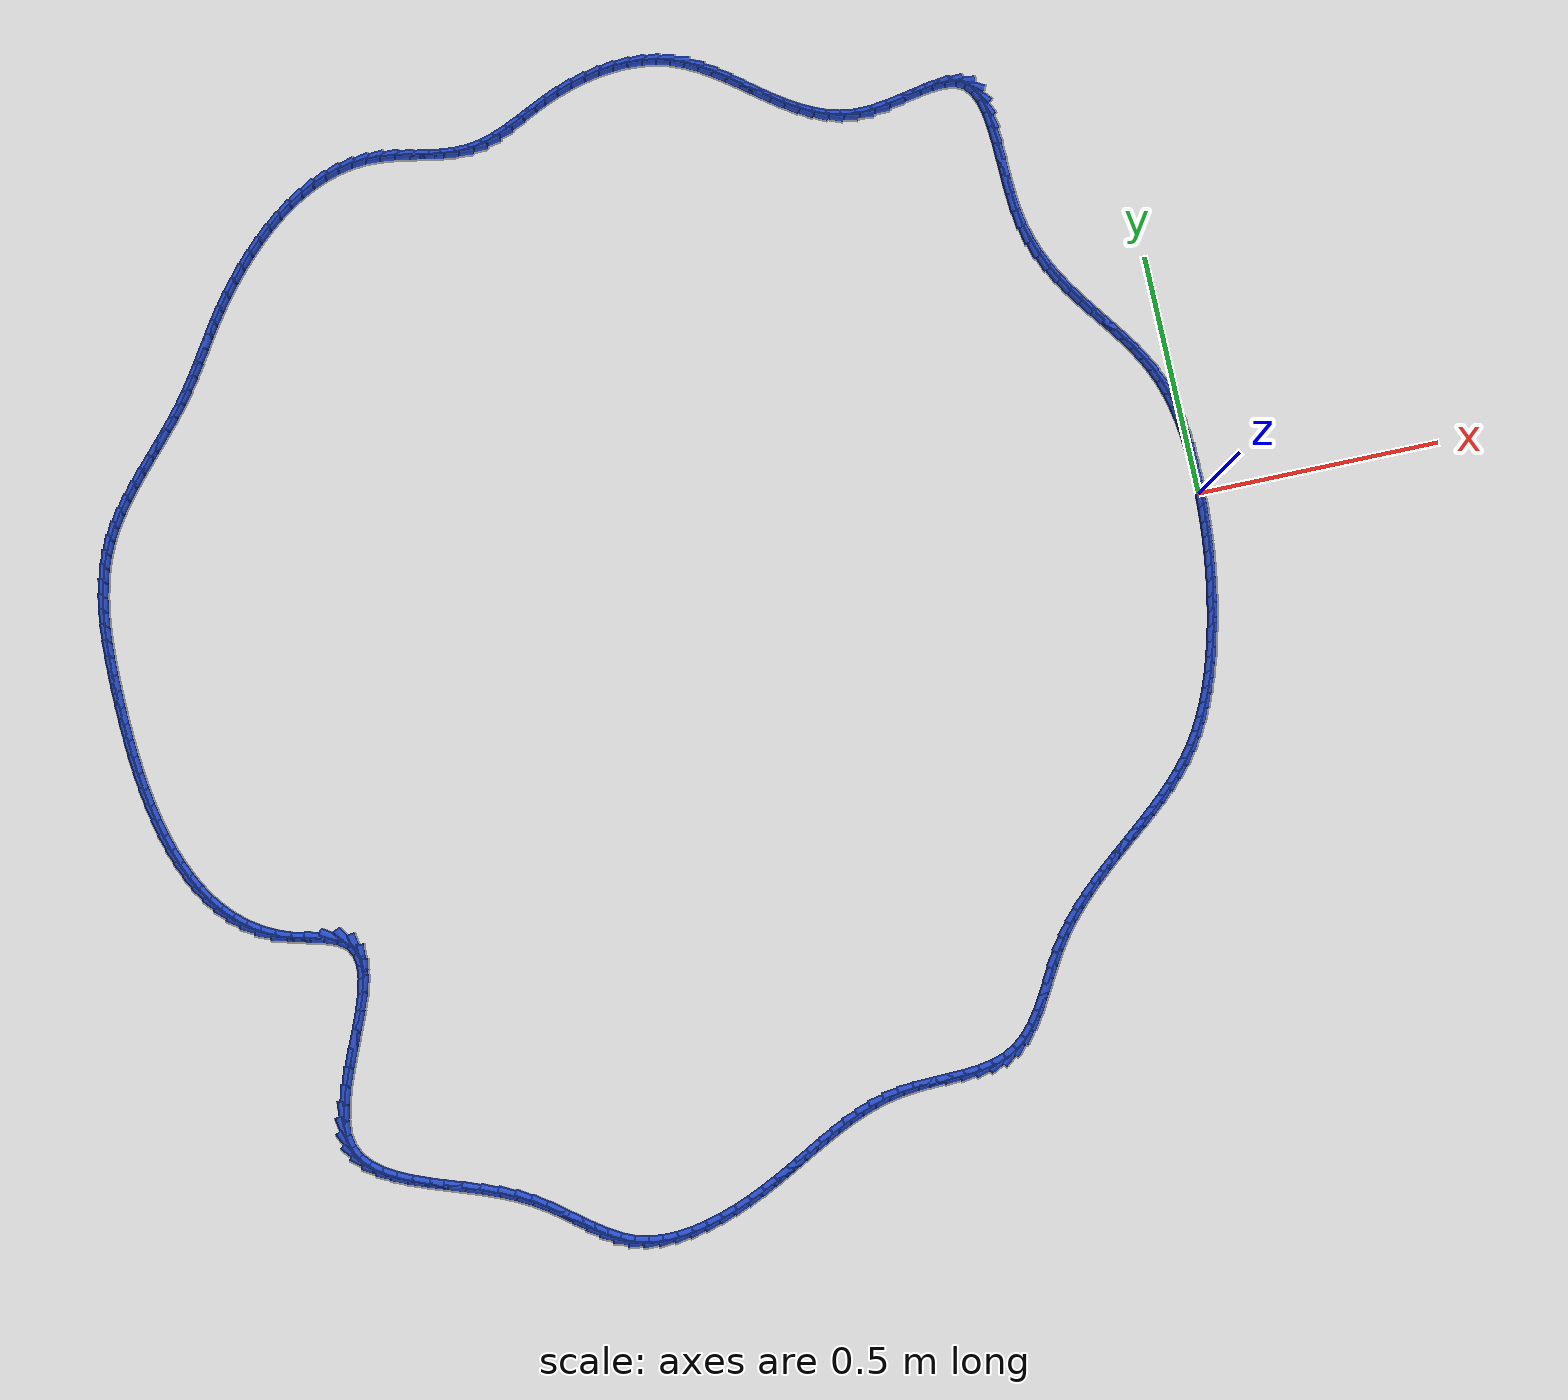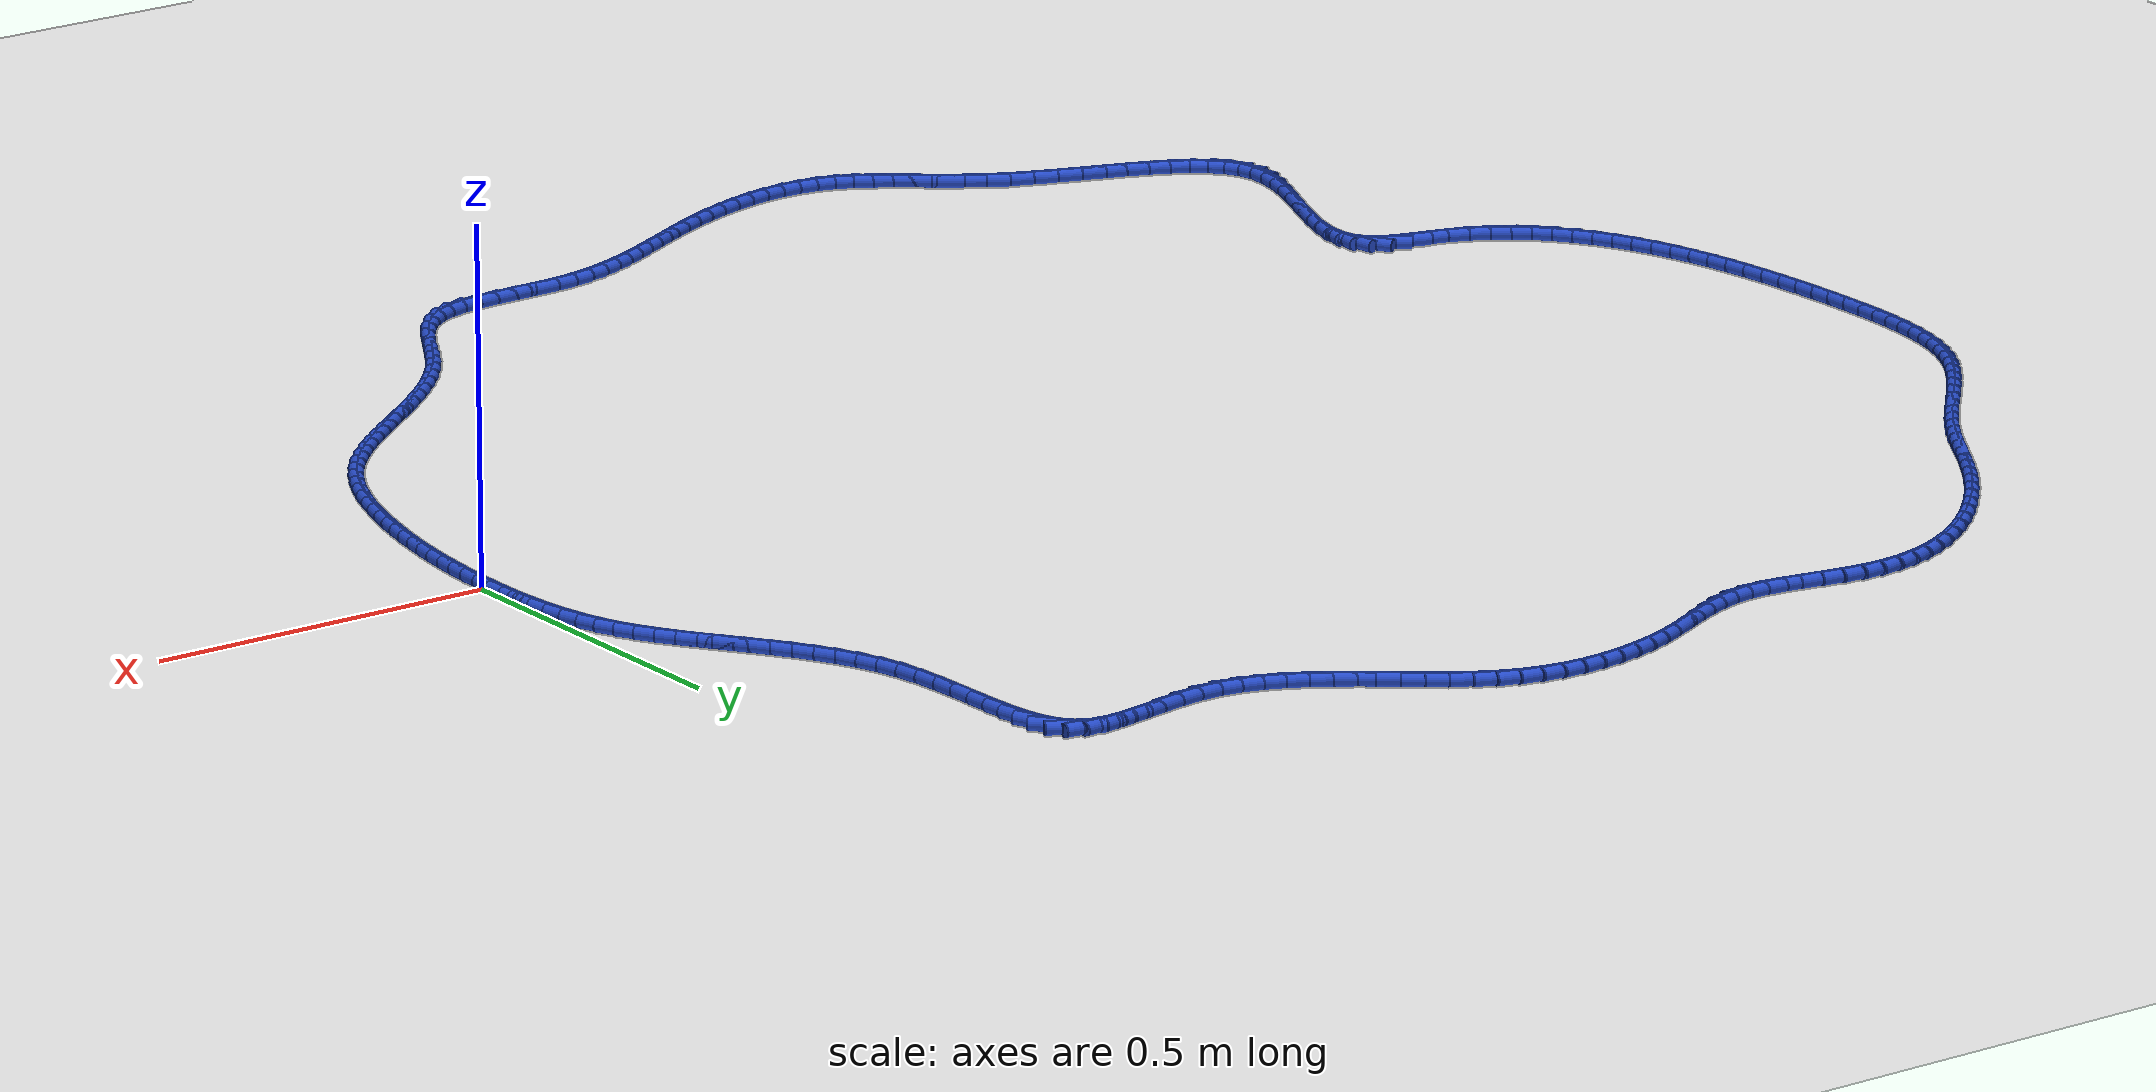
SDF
<sdf version="1.6">
 <world name="default">
  <light name="sun" type="directional">
   <pose>0 0 10 0 -0 0</pose>
   <diffuse>0.8 0.8 0.8 1</diffuse>
   <specular>0.2 0.2 0.2 1</specular>
   <attenuation>
    <range>1000</range>
    <constant>0.9</constant>
    <linear>0.01</linear>
    <quadratic>0.001</quadratic>
   </attenuation>
   <direction>-0.5 0.1 -0.9</direction>
  </light>
  <model name="ground_plane">
   <static>1</static>
   <link name="link">
    <collision name="collision">
     <geometry><plane><normal>0 0 1</normal><size>100 100</size></plane></geometry>
     <surface><friction><ode><mu>100</mu><mu2>50</mu2></ode></friction></surface>
    </collision>
    <visual name="visual">
     <cast_shadows>0</cast_shadows>
     <geometry><plane><normal>0 0 1</normal><size>100 100</size></plane></geometry>
     <material>
      <script><uri>file://media/materials/scripts/gazebo.material</uri><name>Gazebo/WhiteGlow</name></script>
     </material>
    </visual>
   </link>
  </model>
  <gravity>0 0 -9.8</gravity>
  <magnetic_field>6e-06 2.3e-05 -4.2e-05</magnetic_field>
  <atmosphere type="adiabatic"/>
  <physics name="default_physics" default="0" type="ode">
   <max_step_size>0.001</max_step_size>
   <real_time_factor>1</real_time_factor>
   <real_time_update_rate>1000</real_time_update_rate>
  </physics>
  <scene><ambient>0.4 0.4 0.4 1</ambient><background>0.7 0.7 0.7 1</background><shadows>1</shadows></scene>
  <spherical_coordinates>
   <surface_model>EARTH_WGS84</surface_model>
   <latitude_deg>0</latitude_deg>
   <longitude_deg>0</longitude_deg>
   <elevation>0</elevation>
   <heading_deg>0</heading_deg>
  </spherical_coordinates>
  <model name="line">
   <link name="link_0">
    <pose>2.2551405187698492e-17 -4.163336342344337e-17 0.01 0 1.57 1.5498781008881979</pose>
    <collision name="collision">
     <geometry><cylinder><radius>0.01</radius><length>0.08</length></cylinder></geometry>
    </collision>
    <visual name="visual">
     <material>
      <script><name>Gazebo/Blue</name><uri>file://media/materials/scripts/gazebo.material</uri></script>
     </material>
     <geometry><cylinder><radius>0.01</radius><length>0.08</length></cylinder></geometry>
    </visual>
   </link>
   <link name="link_1">
    <pose>0.000653380118124969 0.031230412078863626 0.01 0 1.57 -1.5650343919891607</pose>
    <collision name="collision">
     <geometry><cylinder><radius>0.01</radius><length>0.08</length></cylinder></geometry>
    </collision>
    <visual name="visual">
     <material>
      <script><name>Gazebo/Blue</name><uri>file://media/materials/scripts/gazebo.material</uri></script>
     </material>
     <geometry><cylinder><radius>0.01</radius><length>0.08</length></cylinder></geometry>
    </visual>
   </link>
   <link name="link_2">
    <pose>0.0004725824035189479 0.06260801697644736 0.01 0 1.57 -1.5326680460943594</pose>
    <collision name="collision">
     <geometry><cylinder><radius>0.01</radius><length>0.08</length></cylinder></geometry>
    </collision>
    <visual name="visual">
     <material>
      <script><name>Gazebo/Blue</name><uri>file://media/materials/scripts/gazebo.material</uri></script>
     </material>
     <geometry><cylinder><radius>0.01</radius><length>0.08</length></cylinder></geometry>
    </visual>
   </link>
   <link name="link_3">
    <pose>-0.000722959943697642 0.0939486104392704 0.01 0 1.57 -1.4941184994613455</pose>
    <collision name="collision">
     <geometry><cylinder><radius>0.01</radius><length>0.08</length></cylinder></geometry>
    </collision>
    <visual name="visual">
     <material>
      <script><name>Gazebo/Blue</name><uri>file://media/materials/scripts/gazebo.material</uri></script>
     </material>
     <geometry><cylinder><radius>0.01</radius><length>0.08</length></cylinder></geometry>
    </visual>
   </link>
   <link name="link_4">
    <pose>-0.0031138137234044076 0.12506798821385204 0.01 0 1.57 -1.4487665864710637</pose>
    <collision name="collision">
     <geometry><cylinder><radius>0.01</radius><length>0.08</length></cylinder></geometry>
    </collision>
    <visual name="visual">
     <material>
      <script><name>Gazebo/Blue</name><uri>file://media/materials/scripts/gazebo.material</uri></script>
     </material>
     <geometry><cylinder><radius>0.01</radius><length>0.08</length></cylinder></geometry>
    </visual>
   </link>
   <link name="link_5">
    <pose>-0.006880545735480947 0.15578194604671153 0.01 0 1.57 -1.3958949804898455</pose>
    <collision name="collision">
     <geometry><cylinder><radius>0.01</radius><length>0.08</length></cylinder></geometry>
    </collision>
    <visual name="visual">
     <material>
      <script><name>Gazebo/Blue</name><uri>file://media/materials/scripts/gazebo.material</uri></script>
     </material>
     <geometry><cylinder><radius>0.01</radius><length>0.08</length></cylinder></geometry>
    </visual>
   </link>
   <link name="link_6">
    <pose>-0.012203722779806872 0.18590627968436815 0.01 0 1.57 -1.3347337859105304</pose>
    <collision name="collision">
     <geometry><cylinder><radius>0.01</radius><length>0.08</length></cylinder></geometry>
    </collision>
    <visual name="visual">
     <material>
      <script><name>Gazebo/Blue</name><uri>file://media/materials/scripts/gazebo.material</uri></script>
     </material>
     <geometry><cylinder><radius>0.01</radius><length>0.08</length></cylinder></geometry>
    </visual>
   </link>
   <link name="link_7">
    <pose>-0.019263911656261786 0.21525678487334116 0.01 0 1.57 -1.2645420316985967</pose>
    <collision name="collision">
     <geometry><cylinder><radius>0.01</radius><length>0.08</length></cylinder></geometry>
    </collision>
    <visual name="visual">
     <material>
      <script><name>Gazebo/Blue</name><uri>file://media/materials/scripts/gazebo.material</uri></script>
     </material>
     <geometry><cylinder><radius>0.01</radius><length>0.08</length></cylinder></geometry>
    </visual>
   </link>
   <link name="link_8">
    <pose>-0.028241679164725274 0.2436492573601497 0.01 0 1.57 -1.1850877499780994</pose>
    <collision name="collision">
     <geometry><cylinder><radius>0.01</radius><length>0.08</length></cylinder></geometry>
    </collision>
    <visual name="visual">
     <material>
      <script><name>Gazebo/Blue</name><uri>file://media/materials/scripts/gazebo.material</uri></script>
     </material>
     <geometry><cylinder><radius>0.01</radius><length>0.08</length></cylinder></geometry>
    </visual>
   </link>
   <link name="link_9">
    <pose>-0.03930927444453318 0.2709061761641429 0.01 0 1.57 -1.1067693629343822</pose>
    <collision name="collision">
     <geometry><cylinder><radius>0.01</radius><length>0.08</length></cylinder></geometry>
    </collision>
    <visual name="visual">
     <material>
      <script><name>Gazebo/Blue</name><uri>file://media/materials/scripts/gazebo.material</uri></script>
     </material>
     <geometry><cylinder><radius>0.01</radius><length>0.08</length></cylinder></geometry>
    </visual>
   </link>
   <link name="link_10">
    <pose>-0.05239257530659287 0.29704798063217674 0.01 0 1.57 -1.0427040034742876</pose>
    <collision name="collision">
     <geometry><cylinder><radius>0.01</radius><length>0.08</length></cylinder></geometry>
    </collision>
    <visual name="visual">
     <material>
      <script><name>Gazebo/Blue</name><uri>file://media/materials/scripts/gazebo.material</uri></script>
     </material>
     <geometry><cylinder><radius>0.01</radius><length>0.08</length></cylinder></geometry>
    </visual>
   </link>
   <link name="link_11">
    <pose>-0.06713595193655919 0.32232130259075104 0.01 0 1.57 -0.9943941034914048</pose>
    <collision name="collision">
     <geometry><cylinder><radius>0.01</radius><length>0.08</length></cylinder></geometry>
    </collision>
    <visual name="visual">
     <material>
      <script><name>Gazebo/Blue</name><uri>file://media/materials/scripts/gazebo.material</uri></script>
     </material>
     <geometry><cylinder><radius>0.01</radius><length>0.08</length></cylinder></geometry>
    </visual>
   </link>
   <link name="link_12">
    <pose>-0.08316839042242219 0.34698513504910466 0.01 0 1.57 -0.961973380178026</pose>
    <collision name="collision">
     <geometry><cylinder><radius>0.01</radius><length>0.08</length></cylinder></geometry>
    </collision>
    <visual name="visual">
     <material>
      <script><name>Gazebo/Blue</name><uri>file://media/materials/scripts/gazebo.material</uri></script>
     </material>
     <geometry><cylinder><radius>0.01</radius><length>0.08</length></cylinder></geometry>
    </visual>
   </link>
   <link name="link_13">
    <pose>-0.10011887685217181 0.3712984710164756 0.01 0 1.57 -0.9452034489846207</pose>
    <collision name="collision">
     <geometry><cylinder><radius>0.01</radius><length>0.08</length></cylinder></geometry>
    </collision>
    <visual name="visual">
     <material>
      <script><name>Gazebo/Blue</name><uri>file://media/materials/scripts/gazebo.material</uri></script>
     </material>
     <geometry><cylinder><radius>0.01</radius><length>0.08</length></cylinder></geometry>
    </visual>
   </link>
   <link name="link_14">
    <pose>-0.11761639731379814 0.39552030350210265 0.01 0 1.57 -0.9437224694510126</pose>
    <collision name="collision">
     <geometry><cylinder><radius>0.01</radius><length>0.08</length></cylinder></geometry>
    </collision>
    <visual name="visual">
     <material>
      <script><name>Gazebo/Blue</name><uri>file://media/materials/scripts/gazebo.material</uri></script>
     </material>
     <geometry><cylinder><radius>0.01</radius><length>0.08</length></cylinder></geometry>
    </visual>
   </link>
   <link name="link_15">
    <pose>-0.13528993789529106 0.419909625515224 0.01 0 1.57 -0.9571693902330888</pose>
    <collision name="collision">
     <geometry><cylinder><radius>0.01</radius><length>0.08</length></cylinder></geometry>
    </collision>
    <visual name="visual">
     <material>
      <script><name>Gazebo/Blue</name><uri>file://media/materials/scripts/gazebo.material</uri></script>
     </material>
     <geometry><cylinder><radius>0.01</radius><length>0.08</length></cylinder></geometry>
    </visual>
   </link>
   <link name="link_16">
    <pose>-0.1527684846846408 0.44472543006507825 0.01 0 1.57 -0.9851951102135572</pose>
    <collision name="collision">
     <geometry><cylinder><radius>0.01</radius><length>0.08</length></cylinder></geometry>
    </collision>
    <visual name="visual">
     <material>
      <script><name>Gazebo/Blue</name><uri>file://media/materials/scripts/gazebo.material</uri></script>
     </material>
     <geometry><cylinder><radius>0.01</radius><length>0.08</length></cylinder></geometry>
    </visual>
   </link>
   <link name="link_17">
    <pose>-0.16968102376983712 0.4702267101609035 0.01 0 1.57 -1.0273775265603264</pose>
    <collision name="collision">
     <geometry><cylinder><radius>0.01</radius><length>0.08</length></cylinder></geometry>
    </collision>
    <visual name="visual">
     <material>
      <script><name>Gazebo/Blue</name><uri>file://media/materials/scripts/gazebo.material</uri></script>
     </material>
     <geometry><cylinder><radius>0.01</radius><length>0.08</length></cylinder></geometry>
    </visual>
   </link>
   <link name="link_18">
    <pose>-0.18565654123887018 0.49667245881193844 0.01 0 1.57 -1.083059446885211</pose>
    <collision name="collision">
     <geometry><cylinder><radius>0.01</radius><length>0.08</length></cylinder></geometry>
    </collision>
    <visual name="visual">
     <material>
      <script><name>Gazebo/Blue</name><uri>file://media/materials/scripts/gazebo.material</uri></script>
     </material>
     <geometry><cylinder><radius>0.01</radius><length>0.08</length></cylinder></geometry>
    </visual>
   </link>
   <link name="link_19">
    <pose>-0.20032402317972994 0.5243216690274213 0.01 0 1.57 -1.1511411305950747</pose>
    <collision name="collision">
     <geometry><cylinder><radius>0.01</radius><length>0.08</length></cylinder></geometry>
    </collision>
    <visual name="visual">
     <material>
      <script><name>Gazebo/Blue</name><uri>file://media/materials/scripts/gazebo.material</uri></script>
     </material>
     <geometry><cylinder><radius>0.01</radius><length>0.08</length></cylinder></geometry>
    </visual>
   </link>
   <link name="link_20">
    <pose>-0.2133124556804064 0.5534333338165908 0.01 0 1.57 -1.2298868734529083</pose>
    <collision name="collision">
     <geometry><cylinder><radius>0.01</radius><length>0.08</length></cylinder></geometry>
    </collision>
    <visual name="visual">
     <material>
      <script><name>Gazebo/Blue</name><uri>file://media/materials/scripts/gazebo.material</uri></script>
     </material>
     <geometry><cylinder><radius>0.01</radius><length>0.08</length></cylinder></geometry>
    </visual>
   </link>
   <link name="link_21">
    <pose>-0.2242508248288896 0.5842664461886848 0.01 0 1.57 -1.316834567938857</pose>
    <collision name="collision">
     <geometry><cylinder><radius>0.01</radius><length>0.08</length></cylinder></geometry>
    </collision>
    <visual name="visual">
     <material>
      <script><name>Gazebo/Blue</name><uri>file://media/materials/scripts/gazebo.material</uri></script>
     </material>
     <geometry><cylinder><radius>0.01</radius><length>0.08</length></cylinder></geometry>
    </visual>
   </link>
   <link name="link_22">
    <pose>-0.23276811671316955 0.6170799991529423 0.01 0 1.57 -1.4069695259916977</pose>
    <collision name="collision">
     <geometry><cylinder><radius>0.01</radius><length>0.08</length></cylinder></geometry>
    </collision>
    <visual name="visual">
     <material>
      <script><name>Gazebo/Blue</name><uri>file://media/materials/scripts/gazebo.material</uri></script>
     </material>
     <geometry><cylinder><radius>0.01</radius><length>0.08</length></cylinder></geometry>
    </visual>
   </link>
   <link name="link_23">
    <pose>-0.2385527625339994 0.652073059883295 0.01 0 1.57 -1.4776716845308662</pose>
    <collision name="collision">
     <geometry><cylinder><radius>0.01</radius><length>0.08</length></cylinder></geometry>
    </collision>
    <visual name="visual">
     <material>
      <script><name>Gazebo/Blue</name><uri>file://media/materials/scripts/gazebo.material</uri></script>
     </material>
     <geometry><cylinder><radius>0.01</radius><length>0.08</length></cylinder></geometry>
    </visual>
   </link>
   <link name="link_24">
    <pose>-0.2419785516439821 0.6887537950267123 0.01 0 1.57 -1.5206108015041493</pose>
    <collision name="collision">
     <geometry><cylinder><radius>0.01</radius><length>0.08</length></cylinder></geometry>
    </collision>
    <visual name="visual">
     <material>
      <script><name>Gazebo/Blue</name><uri>file://media/materials/scripts/gazebo.material</uri></script>
     </material>
     <geometry><cylinder><radius>0.01</radius><length>0.08</length></cylinder></geometry>
    </visual>
   </link>
   <link name="link_25">
    <pose>-0.2438587524204318 0.7261873382131283 0.01 0 1.57 -1.5397924425745155</pose>
    <collision name="collision">
     <geometry><cylinder><radius>0.01</radius><length>0.08</length></cylinder></geometry>
    </collision>
    <visual name="visual">
     <material>
      <script><name>Gazebo/Blue</name><uri>file://media/materials/scripts/gazebo.material</uri></script>
     </material>
     <geometry><cylinder><radius>0.01</radius><length>0.08</length></cylinder></geometry>
    </visual>
   </link>
   <link name="link_26">
    <pose>-0.24501383808825647 0.7634315599605046 0.01 0 1.57 -1.536184072782006</pose>
    <collision name="collision">
     <geometry><cylinder><radius>0.01</radius><length>0.08</length></cylinder></geometry>
    </collision>
    <visual name="visual">
     <material>
      <script><name>Gazebo/Blue</name><uri>file://media/materials/scripts/gazebo.material</uri></script>
     </material>
     <geometry><cylinder><radius>0.01</radius><length>0.08</length></cylinder></geometry>
    </visual>
   </link>
   <link name="link_27">
    <pose>-0.24626428187236388 0.7995443307868023 0.01 0 1.57 -1.5072414178572693</pose>
    <collision name="collision">
     <geometry><cylinder><radius>0.01</radius><length>0.08</length></cylinder></geometry>
    </collision>
    <visual name="visual">
     <material>
      <script><name>Gazebo/Blue</name><uri>file://media/materials/scripts/gazebo.material</uri></script>
     </material>
     <geometry><cylinder><radius>0.01</radius><length>0.08</length></cylinder></geometry>
    </visual>
   </link>
   <link name="link_28">
    <pose>-0.24843055699766195 0.8335835212099827 0.01 0 1.57 -1.4456592440203297</pose>
    <collision name="collision">
     <geometry><cylinder><radius>0.01</radius><length>0.08</length></cylinder></geometry>
    </collision>
    <visual name="visual">
     <material>
      <script><name>Gazebo/Blue</name><uri>file://media/materials/scripts/gazebo.material</uri></script>
     </material>
     <geometry><cylinder><radius>0.01</radius><length>0.08</length></cylinder></geometry>
    </visual>
   </link>
   <link name="link_29">
    <pose>-0.2523331366890584 0.8646070017480069 0.01 0 1.57 -1.3365232402149478</pose>
    <collision name="collision">
     <geometry><cylinder><radius>0.01</radius><length>0.08</length></cylinder></geometry>
    </collision>
    <visual name="visual">
     <material>
      <script><name>Gazebo/Blue</name><uri>file://media/materials/scripts/gazebo.material</uri></script>
     </material>
     <geometry><cylinder><radius>0.01</radius><length>0.08</length></cylinder></geometry>
    </visual>
   </link>
   <link name="link_30">
    <pose>-0.25879249417146105 0.8916726429188356 0.01 0 1.57 -1.1531297521584396</pose>
    <collision name="collision">
     <geometry><cylinder><radius>0.01</radius><length>0.08</length></cylinder></geometry>
    </collision>
    <visual name="visual">
     <material>
      <script><name>Gazebo/Blue</name><uri>file://media/materials/scripts/gazebo.material</uri></script>
     </material>
     <geometry><cylinder><radius>0.01</radius><length>0.08</length></cylinder></geometry>
    </visual>
   </link>
   <link name="link_31">
    <pose>-0.2686291026697778 0.9138383152404306 0.01 0 1.57 -0.8606641168503186</pose>
    <collision name="collision">
     <geometry><cylinder><radius>0.01</radius><length>0.08</length></cylinder></geometry>
    </collision>
    <visual name="visual">
     <material>
      <script><name>Gazebo/Blue</name><uri>file://media/materials/scripts/gazebo.material</uri></script>
     </material>
     <geometry><cylinder><radius>0.01</radius><length>0.08</length></cylinder></geometry>
    </visual>
   </link>
   <link name="link_32">
    <pose>-0.28266343540891653 0.9301618892307528 0.01 0 1.57 -0.4656129992218823</pose>
    <collision name="collision">
     <geometry><cylinder><radius>0.01</radius><length>0.08</length></cylinder></geometry>
    </collision>
    <visual name="visual">
     <material>
      <script><name>Gazebo/Blue</name><uri>file://media/materials/scripts/gazebo.material</uri></script>
     </material>
     <geometry><cylinder><radius>0.01</radius><length>0.08</length></cylinder></geometry>
    </visual>
   </link>
   <link name="link_33">
    <pose>-0.3016985785636309 0.9397262712240156 0.01 0 1.57 -0.12286702648049602</pose>
    <collision name="collision">
     <geometry><cylinder><radius>0.01</radius><length>0.08</length></cylinder></geometry>
    </collision>
    <visual name="visual">
     <material>
      <script><name>Gazebo/Blue</name><uri>file://media/materials/scripts/gazebo.material</uri></script>
     </material>
     <geometry><cylinder><radius>0.01</radius><length>0.08</length></cylinder></geometry>
    </visual>
   </link>
   <link name="link_34">
    <pose>-0.3257833309527112 0.9427004747133781 0.01 0 1.57 0.06975178542649269</pose>
    <collision name="collision">
     <geometry><cylinder><radius>0.01</radius><length>0.08</length></cylinder></geometry>
    </collision>
    <visual name="visual">
     <material>
      <script><name>Gazebo/Blue</name><uri>file://media/materials/scripts/gazebo.material</uri></script>
     </material>
     <geometry><cylinder><radius>0.01</radius><length>0.08</length></cylinder></geometry>
    </visual>
   </link>
   <link name="link_35">
    <pose>-0.3539387333841534 0.9407333939355419 0.01 0 1.57 0.16382966223878545</pose>
    <collision name="collision">
     <geometry><cylinder><radius>0.01</radius><length>0.08</length></cylinder></geometry>
    </collision>
    <visual name="visual">
     <material>
      <script><name>Gazebo/Blue</name><uri>file://media/materials/scripts/gazebo.material</uri></script>
     </material>
     <geometry><cylinder><radius>0.01</radius><length>0.08</length></cylinder></geometry>
    </visual>
   </link>
   <link name="link_36">
    <pose>-0.3851120993172481 0.9355800839962793 0.01 0 1.57 0.1961404768771493</pose>
    <collision name="collision">
     <geometry><cylinder><radius>0.01</radius><length>0.08</length></cylinder></geometry>
    </collision>
    <visual name="visual">
     <material>
      <script><name>Gazebo/Blue</name><uri>file://media/materials/scripts/gazebo.material</uri></script>
     </material>
     <geometry><cylinder><radius>0.01</radius><length>0.08</length></cylinder></geometry>
    </visual>
   </link>
   <link name="link_37">
    <pose>-0.41825074221128666 0.9289956000013634 0.01 0 1.57 0.18182765332703554</pose>
    <collision name="collision">
     <geometry><cylinder><radius>0.01</radius><length>0.08</length></cylinder></geometry>
    </collision>
    <visual name="visual">
     <material>
      <script><name>Gazebo/Blue</name><uri>file://media/materials/scripts/gazebo.material</uri></script>
     </material>
     <geometry><cylinder><radius>0.01</radius><length>0.08</length></cylinder></geometry>
    </visual>
   </link>
   <link name="link_38">
    <pose>-0.4523019755255591 0.9227349970565661 0.01 0 1.57 0.12269310326697963</pose>
    <collision name="collision">
     <geometry><cylinder><radius>0.01</radius><length>0.08</length></cylinder></geometry>
    </collision>
    <visual name="visual">
     <material>
      <script><name>Gazebo/Blue</name><uri>file://media/materials/scripts/gazebo.material</uri></script>
     </material>
     <geometry><cylinder><radius>0.01</radius><length>0.08</length></cylinder></geometry>
    </visual>
   </link>
   <link name="link_39">
    <pose>-0.48621311271935697 0.918553330267661 0.01 0 1.57 0.01132102907444683</pose>
    <collision name="collision">
     <geometry><cylinder><radius>0.01</radius><length>0.08</length></cylinder></geometry>
    </collision>
    <visual name="visual">
     <material>
      <script><name>Gazebo/Blue</name><uri>file://media/materials/scripts/gazebo.material</uri></script>
     </material>
     <geometry><cylinder><radius>0.01</radius><length>0.08</length></cylinder></geometry>
    </visual>
   </link>
   <link name="link_40">
    <pose>-0.518943744233631 0.9181827700054892 0.01 0 1.57 -0.1347020902670538</pose>
    <collision name="collision">
     <geometry><cylinder><radius>0.01</radius><length>0.08</length></cylinder></geometry>
    </collision>
    <visual name="visual">
     <material>
      <script><name>Gazebo/Blue</name><uri>file://media/materials/scripts/gazebo.material</uri></script>
     </material>
     <geometry><cylinder><radius>0.01</radius><length>0.08</length></cylinder></geometry>
    </visual>
   </link>
   <link name="link_41">
    <pose>-0.5499725529725472 0.9223878796382923 0.01 0 1.57 -0.2723756701730962</pose>
    <collision name="collision">
     <geometry><cylinder><radius>0.01</radius><length>0.08</length></cylinder></geometry>
    </collision>
    <visual name="visual">
     <material>
      <script><name>Gazebo/Blue</name><uri>file://media/materials/scripts/gazebo.material</uri></script>
     </material>
     <geometry><cylinder><radius>0.01</radius><length>0.08</length></cylinder></geometry>
    </visual>
   </link>
   <link name="link_42">
    <pose>-0.579477787620839 0.9306292067836939 0.01 0 1.57 -0.3915296969777729</pose>
    <collision name="collision">
     <geometry><cylinder><radius>0.01</radius><length>0.08</length></cylinder></geometry>
    </collision>
    <visual name="visual">
     <material>
      <script><name>Gazebo/Blue</name><uri>file://media/materials/scripts/gazebo.material</uri></script>
     </material>
     <geometry><cylinder><radius>0.01</radius><length>0.08</length></cylinder></geometry>
    </visual>
   </link>
   <link name="link_43">
    <pose>-0.6076870788718 0.9422752492210549 0.01 0 1.57 -0.4883514980227821</pose>
    <collision name="collision">
     <geometry><cylinder><radius>0.01</radius><length>0.08</length></cylinder></geometry>
    </collision>
    <visual name="visual">
     <material>
      <script><name>Gazebo/Blue</name><uri>file://media/materials/scripts/gazebo.material</uri></script>
     </material>
     <geometry><cylinder><radius>0.01</radius><length>0.08</length></cylinder></geometry>
    </visual>
   </link>
   <link name="link_44">
    <pose>-0.6348280574187213 0.9566945047297342 0.01 0 1.57 -0.5619629587354771</pose>
    <collision name="collision">
     <geometry><cylinder><radius>0.01</radius><length>0.08</length></cylinder></geometry>
    </collision>
    <visual name="visual">
     <material>
      <script><name>Gazebo/Blue</name><uri>file://media/materials/scripts/gazebo.material</uri></script>
     </material>
     <geometry><cylinder><radius>0.01</radius><length>0.08</length></cylinder></geometry>
    </visual>
   </link>
   <link name="link_45">
    <pose>-0.6611283539548961 0.9732554710890924 0.01 0 1.57 -0.6130762529158269</pose>
    <collision name="collision">
     <geometry><cylinder><radius>0.01</radius><length>0.08</length></cylinder></geometry>
    </collision>
    <visual name="visual">
     <material>
      <script><name>Gazebo/Blue</name><uri>file://media/materials/scripts/gazebo.material</uri></script>
     </material>
     <geometry><cylinder><radius>0.01</radius><length>0.08</length></cylinder></geometry>
    </visual>
   </link>
   <link name="link_46">
    <pose>-0.6868155991736159 0.9913266460784883 0.01 0 1.57 -0.6428307923180901</pose>
    <collision name="collision">
     <geometry><cylinder><radius>0.01</radius><length>0.08</length></cylinder></geometry>
    </collision>
    <visual name="visual">
     <material>
      <script><name>Gazebo/Blue</name><uri>file://media/materials/scripts/gazebo.material</uri></script>
     </material>
     <geometry><cylinder><radius>0.01</radius><length>0.08</length></cylinder></geometry>
    </visual>
   </link>
   <link name="link_47">
    <pose>-0.712117423768174 1.0102765274772831 0.01 0 1.57 -0.6520756011382788</pose>
    <collision name="collision">
     <geometry><cylinder><radius>0.01</radius><length>0.08</length></cylinder></geometry>
    </collision>
    <visual name="visual">
     <material>
      <script><name>Gazebo/Blue</name><uri>file://media/materials/scripts/gazebo.material</uri></script>
     </material>
     <geometry><cylinder><radius>0.01</radius><length>0.08</length></cylinder></geometry>
    </visual>
   </link>
   <link name="link_48">
    <pose>-0.737261458431862 1.0294736130648356 0.01 0 1.57 -0.6410186518004736</pose>
    <collision name="collision">
     <geometry><cylinder><radius>0.01</radius><length>0.08</length></cylinder></geometry>
    </collision>
    <visual name="visual">
     <material>
      <script><name>Gazebo/Blue</name><uri>file://media/materials/scripts/gazebo.material</uri></script>
     </material>
     <geometry><cylinder><radius>0.01</radius><length>0.08</length></cylinder></geometry>
    </visual>
   </link>
   <link name="link_49">
    <pose>-0.7624753338579725 1.048286400620506 0.01 0 1.57 -0.6091205736839094</pose>
    <collision name="collision">
     <geometry><cylinder><radius>0.01</radius><length>0.08</length></cylinder></geometry>
    </collision>
    <visual name="visual">
     <material>
      <script><name>Gazebo/Blue</name><uri>file://media/materials/scripts/gazebo.material</uri></script>
     </material>
     <geometry><cylinder><radius>0.01</radius><length>0.08</length></cylinder></geometry>
    </visual>
   </link>
   <link name="link_50">
    <pose>-0.7879866807397977 1.0660833879236542 0.01 0 1.57 -0.555192303690817</pose>
    <collision name="collision">
     <geometry><cylinder><radius>0.01</radius><length>0.08</length></cylinder></geometry>
    </collision>
    <visual name="visual">
     <material>
      <script><name>Gazebo/Blue</name><uri>file://media/materials/scripts/gazebo.material</uri></script>
     </material>
     <geometry><cylinder><radius>0.01</radius><length>0.08</length></cylinder></geometry>
    </visual>
   </link>
   <link name="link_51">
    <pose>-0.81402312977063 1.0822330727536398 0.01 0 1.57 -0.47776956233142653</pose>
    <collision name="collision">
     <geometry><cylinder><radius>0.01</radius><length>0.08</length></cylinder></geometry>
    </collision>
    <visual name="visual">
     <material>
      <script><name>Gazebo/Blue</name><uri>file://media/materials/scripts/gazebo.material</uri></script>
     </material>
     <geometry><cylinder><radius>0.01</radius><length>0.08</length></cylinder></geometry>
    </visual>
   </link>
   <link name="link_52">
    <pose>-0.8408123116437618 1.0961039528898229 0.01 0 1.57 -0.3759300105695635</pose>
    <collision name="collision">
     <geometry><cylinder><radius>0.01</radius><length>0.08</length></cylinder></geometry>
    </collision>
    <visual name="visual">
     <material>
      <script><name>Gazebo/Blue</name><uri>file://media/materials/scripts/gazebo.material</uri></script>
     </material>
     <geometry><cylinder><radius>0.01</radius><length>0.08</length></cylinder></geometry>
    </visual>
   </link>
   <link name="link_53">
    <pose>-0.8685818135669047 1.10706460522726 0.01 0 1.57 -0.2572716047854708</pose>
    <collision name="collision">
     <geometry><cylinder><radius>0.01</radius><length>0.08</length></cylinder></geometry>
    </collision>
    <visual name="visual">
     <material>
      <script><name>Gazebo/Blue</name><uri>file://media/materials/scripts/gazebo.material</uri></script>
     </material>
     <geometry><cylinder><radius>0.01</radius><length>0.08</length></cylinder></geometry>
    </visual>
   </link>
   <link name="link_54">
    <pose>-0.8974607726945923 1.1146627222310221 0.01 0 1.57 -0.14469863775050495</pose>
    <collision name="collision">
     <geometry><cylinder><radius>0.01</radius><length>0.08</length></cylinder></geometry>
    </collision>
    <visual name="visual">
     <material>
      <script><name>Gazebo/Blue</name><uri>file://media/materials/scripts/gazebo.material</uri></script>
     </material>
     <geometry><cylinder><radius>0.01</radius><length>0.08</length></cylinder></geometry>
    </visual>
   </link>
   <link name="link_55">
    <pose>-0.9272702626208903 1.1190064732623572 0.01 0 1.57 -0.042821099001261576</pose>
    <collision name="collision">
     <geometry><cylinder><radius>0.01</radius><length>0.08</length></cylinder></geometry>
    </collision>
    <visual name="visual">
     <material>
      <script><name>Gazebo/Blue</name><uri>file://media/materials/scripts/gazebo.material</uri></script>
     </material>
     <geometry><cylinder><radius>0.01</radius><length>0.08</length></cylinder></geometry>
    </visual>
   </link>
   <link name="link_56">
    <pose>-0.9577712637361671 1.1203133585369607 0.01 0 1.57 0.04882415933560241</pose>
    <collision name="collision">
     <geometry><cylinder><radius>0.01</radius><length>0.08</length></cylinder></geometry>
    </collision>
    <visual name="visual">
     <material>
      <script><name>Gazebo/Blue</name><uri>file://media/materials/scripts/gazebo.material</uri></script>
     </material>
     <geometry><cylinder><radius>0.01</radius><length>0.08</length></cylinder></geometry>
    </visual>
   </link>
   <link name="link_57">
    <pose>-0.9887247564307903 1.118800878270528 0.01 0 1.57 0.13125091852050708</pose>
    <collision name="collision">
     <geometry><cylinder><radius>0.01</radius><length>0.08</length></cylinder></geometry>
    </collision>
    <visual name="visual">
     <material>
      <script><name>Gazebo/Blue</name><uri>file://media/materials/scripts/gazebo.material</uri></script>
     </material>
     <geometry><cylinder><radius>0.01</radius><length>0.08</length></cylinder></geometry>
    </visual>
   </link>
   <link name="link_58">
    <pose>-1.0198917210951282 1.1146865326787536 0.01 0 1.57 0.20573129876810364</pose>
    <collision name="collision">
     <geometry><cylinder><radius>0.01</radius><length>0.08</length></cylinder></geometry>
    </collision>
    <visual name="visual">
     <material>
      <script><name>Gazebo/Blue</name><uri>file://media/materials/scripts/gazebo.material</uri></script>
     </material>
     <geometry><cylinder><radius>0.01</radius><length>0.08</length></cylinder></geometry>
    </visual>
   </link>
   <link name="link_59">
    <pose>-1.0510331381195483 1.1081878219773333 0.01 0 1.57 0.27361097702413645</pose>
    <collision name="collision">
     <geometry><cylinder><radius>0.01</radius><length>0.08</length></cylinder></geometry>
    </collision>
    <visual name="visual">
     <material>
      <script><name>Gazebo/Blue</name><uri>file://media/materials/scripts/gazebo.material</uri></script>
     </material>
     <geometry><cylinder><radius>0.01</radius><length>0.08</length></cylinder></geometry>
    </visual>
   </link>
   <link name="link_60">
    <pose>-1.0819099878944192 1.0995222463819616 0.01 0 1.57 0.3362142021863939</pose>
    <collision name="collision">
     <geometry><cylinder><radius>0.01</radius><length>0.08</length></cylinder></geometry>
    </collision>
    <visual name="visual">
     <material>
      <script><name>Gazebo/Blue</name><uri>file://media/materials/scripts/gazebo.material</uri></script>
     </material>
     <geometry><cylinder><radius>0.01</radius><length>0.08</length></cylinder></geometry>
    </visual>
   </link>
   <link name="link_61">
    <pose>-1.112283250810109 1.0889073061083345 0.01 0 1.57 0.3946468472348083</pose>
    <collision name="collision">
     <geometry><cylinder><radius>0.01</radius><length>0.08</length></cylinder></geometry>
    </collision>
    <visual name="visual">
     <material>
      <script><name>Gazebo/Blue</name><uri>file://media/materials/scripts/gazebo.material</uri></script>
     </material>
     <geometry><cylinder><radius>0.01</radius><length>0.08</length></cylinder></geometry>
    </visual>
   </link>
   <link name="link_62">
    <pose>-1.141916818403076 1.0765650035251488 0.01 0 1.57 0.4394264871074744</pose>
    <collision name="collision">
     <geometry><cylinder><radius>0.01</radius><length>0.08</length></cylinder></geometry>
    </collision>
    <visual name="visual">
     <material>
      <script><name>Gazebo/Blue</name><uri>file://media/materials/scripts/gazebo.material</uri></script>
     </material>
     <geometry><cylinder><radius>0.01</radius><length>0.08</length></cylinder></geometry>
    </visual>
   </link>
   <link name="link_63">
    <pose>-1.1707611426341527 1.063005860899622 0.01 0 1.57 0.4538900260257466</pose>
    <collision name="collision">
     <geometry><cylinder><radius>0.01</radius><length>0.08</length></cylinder></geometry>
    </collision>
    <visual name="visual">
     <material>
      <script><name>Gazebo/Blue</name><uri>file://media/materials/scripts/gazebo.material</uri></script>
     </material>
     <geometry><cylinder><radius>0.01</radius><length>0.08</length></cylinder></geometry>
    </visual>
   </link>
   <link name="link_64">
    <pose>-1.1990628973556527 1.0491985143264733 0.01 0 1.57 0.4355872632187543</pose>
    <collision name="collision">
     <geometry><cylinder><radius>0.01</radius><length>0.08</length></cylinder></geometry>
    </collision>
    <visual name="visual">
     <material>
      <script><name>Gazebo/Blue</name><uri>file://media/materials/scripts/gazebo.material</uri></script>
     </material>
     <geometry><cylinder><radius>0.01</radius><length>0.08</length></cylinder></geometry>
    </visual>
   </link>
   <link name="link_65">
    <pose>-1.2270950804445544 1.0361523105975028 0.01 0 1.57 0.38239510337548394</pose>
    <collision name="collision">
     <geometry><cylinder><radius>0.01</radius><length>0.08</length></cylinder></geometry>
    </collision>
    <visual name="visual">
     <material>
      <script><name>Gazebo/Blue</name><uri>file://media/materials/scripts/gazebo.material</uri></script>
     </material>
     <geometry><cylinder><radius>0.01</radius><length>0.08</length></cylinder></geometry>
    </visual>
   </link>
   <link name="link_66">
    <pose>-1.255130689777832 1.0248765965045101 0.01 0 1.57 0.2915302737479753</pose>
    <collision name="collision">
     <geometry><cylinder><radius>0.01</radius><length>0.08</length></cylinder></geometry>
    </collision>
    <visual name="visual">
     <material>
      <script><name>Gazebo/Blue</name><uri>file://media/materials/scripts/gazebo.material</uri></script>
     </material>
     <geometry><cylinder><radius>0.01</radius><length>0.08</length></cylinder></geometry>
    </visual>
   </link>
   <link name="link_67">
    <pose>-1.2834427232324628 1.0163807188392964 0.01 0 1.57 0.16170790497495743</pose>
    <collision name="collision">
     <geometry><cylinder><radius>0.01</radius><length>0.08</length></cylinder></geometry>
    </collision>
    <visual name="visual">
     <material>
      <script><name>Gazebo/Blue</name><uri>file://media/materials/scripts/gazebo.material</uri></script>
     </material>
     <geometry><cylinder><radius>0.01</radius><length>0.08</length></cylinder></geometry>
    </visual>
   </link>
   <link name="link_68">
    <pose>-1.3123038762742474 1.0116725316949333 0.01 0 1.57 0.01643625740724954</pose>
    <collision name="collision">
     <geometry><cylinder><radius>0.01</radius><length>0.08</length></cylinder></geometry>
    </collision>
    <visual name="visual">
     <material>
      <script><name>Gazebo/Blue</name><uri>file://media/materials/scripts/gazebo.material</uri></script>
     </material>
     <geometry><cylinder><radius>0.01</radius><length>0.08</length></cylinder></geometry>
    </visual>
   </link>
   <link name="link_69">
    <pose>-1.341870683514178 1.0111865202742203 0.01 0 1.57 -0.09045481558138192</pose>
    <collision name="collision">
     <geometry><cylinder><radius>0.01</radius><length>0.08</length></cylinder></geometry>
    </collision>
    <visual name="visual">
     <material>
      <script><name>Gazebo/Blue</name><uri>file://media/materials/scripts/gazebo.material</uri></script>
     </material>
     <geometry><cylinder><radius>0.01</radius><length>0.08</length></cylinder></geometry>
    </visual>
   </link>
   <link name="link_70">
    <pose>-1.3720085371938053 1.0139200937739732 0.01 0 1.57 -0.153679985543018</pose>
    <collision name="collision">
     <geometry><cylinder><radius>0.01</radius><length>0.08</length></cylinder></geometry>
    </collision>
    <visual name="visual">
     <material>
      <script><name>Gazebo/Blue</name><uri>file://media/materials/scripts/gazebo.material</uri></script>
     </material>
     <geometry><cylinder><radius>0.01</radius><length>0.08</length></cylinder></geometry>
    </visual>
   </link>
   <link name="link_71">
    <pose>-1.4025379511300267 1.0186491419076829 0.01 0 1.57 -0.1770512199456167</pose>
    <collision name="collision">
     <geometry><cylinder><radius>0.01</radius><length>0.08</length></cylinder></geometry>
    </collision>
    <visual name="visual">
     <material>
      <script><name>Gazebo/Blue</name><uri>file://media/materials/scripts/gazebo.material</uri></script>
     </material>
     <geometry><cylinder><radius>0.01</radius><length>0.08</length></cylinder></geometry>
    </visual>
   </link>
   <link name="link_72">
    <pose>-1.4332794391397405 1.024149554388842 0.01 0 1.57 -0.16257568932504643</pose>
    <collision name="collision">
     <geometry><cylinder><radius>0.01</radius><length>0.08</length></cylinder></geometry>
    </collision>
    <visual name="visual">
     <material>
      <script><name>Gazebo/Blue</name><uri>file://media/materials/scripts/gazebo.material</uri></script>
     </material>
     <geometry><cylinder><radius>0.01</radius><length>0.08</length></cylinder></geometry>
    </visual>
   </link>
   <link name="link_73">
    <pose>-1.4640535150398462 1.0291972209309408 0.01 0 1.57 -0.1096182654560711</pose>
    <collision name="collision">
     <geometry><cylinder><radius>0.01</radius><length>0.08</length></cylinder></geometry>
    </collision>
    <visual name="visual">
     <material>
      <script><name>Gazebo/Blue</name><uri>file://media/materials/scripts/gazebo.material</uri></script>
     </material>
     <geometry><cylinder><radius>0.01</radius><length>0.08</length></cylinder></geometry>
    </visual>
   </link>
   <link name="link_74">
    <pose>-1.4946806926472416 1.0325680312474714 0.01 0 1.57 -0.01614259737857227</pose>
    <collision name="collision">
     <geometry><cylinder><radius>0.01</radius><length>0.08</length></cylinder></geometry>
    </collision>
    <visual name="visual">
     <material>
      <script><name>Gazebo/Blue</name><uri>file://media/materials/scripts/gazebo.material</uri></script>
     </material>
     <geometry><cylinder><radius>0.01</radius><length>0.08</length></cylinder></geometry>
    </visual>
   </link>
   <link name="link_75">
    <pose>-1.5249831169390007 1.033057233575823 0.01 0 1.57 0.09881605148375272</pose>
    <collision name="collision">
     <geometry><cylinder><radius>0.01</radius><length>0.08</length></cylinder></geometry>
    </collision>
    <visual name="visual">
     <material>
      <script><name>Gazebo/Blue</name><uri>file://media/materials/scripts/gazebo.material</uri></script>
     </material>
     <geometry><cylinder><radius>0.01</radius><length>0.08</length></cylinder></geometry>
    </visual>
   </link>
   <link name="link_76">
    <pose>-1.5548366498145625 1.0300975857865686 0.01 0 1.57 0.2084973328072489</pose>
    <collision name="collision">
     <geometry><cylinder><radius>0.01</radius><length>0.08</length></cylinder></geometry>
    </collision>
    <visual name="visual">
     <material>
      <script><name>Gazebo/Blue</name><uri>file://media/materials/scripts/gazebo.material</uri></script>
     </material>
     <geometry><cylinder><radius>0.01</radius><length>0.08</length></cylinder></geometry>
    </visual>
   </link>
   <link name="link_77">
    <pose>-1.5841817919173038 1.023888974992292 0.01 0 1.57 0.309771538604265</pose>
    <collision name="collision">
     <geometry><cylinder><radius>0.01</radius><length>0.08</length></cylinder></geometry>
    </collision>
    <visual name="visual">
     <material>
      <script><name>Gazebo/Blue</name><uri>file://media/materials/scripts/gazebo.material</uri></script>
     </material>
     <geometry><cylinder><radius>0.01</radius><length>0.08</length></cylinder></geometry>
    </visual>
   </link>
   <link name="link_78">
    <pose>-1.612962882899172 1.0146768494590823 0.01 0 1.57 0.4019189414343428</pose>
    <collision name="collision">
     <geometry><cylinder><radius>0.01</radius><length>0.08</length></cylinder></geometry>
    </collision>
    <visual name="visual">
     <material>
      <script><name>Gazebo/Blue</name><uri>file://media/materials/scripts/gazebo.material</uri></script>
     </material>
     <geometry><cylinder><radius>0.01</radius><length>0.08</length></cylinder></geometry>
    </visual>
   </link>
   <link name="link_79">
    <pose>-1.6411242624121138 1.0027066574530294 0.01 0 1.57 0.48494762592276675</pose>
    <collision name="collision">
     <geometry><cylinder><radius>0.01</radius><length>0.08</length></cylinder></geometry>
    </collision>
    <visual name="visual">
     <material>
      <script><name>Gazebo/Blue</name><uri>file://media/materials/scripts/gazebo.material</uri></script>
     </material>
     <geometry><cylinder><radius>0.01</radius><length>0.08</length></cylinder></geometry>
    </visual>
   </link>
   <link name="link_80">
    <pose>-1.6686102701080767 0.9882238472402233 0.01 0 1.57 0.5593547596269517</pose>
    <collision name="collision">
     <geometry><cylinder><radius>0.01</radius><length>0.08</length></cylinder></geometry>
    </collision>
    <visual name="visual">
     <material>
      <script><name>Gazebo/Blue</name><uri>file://media/materials/scripts/gazebo.material</uri></script>
     </material>
     <geometry><cylinder><radius>0.01</radius><length>0.08</length></cylinder></geometry>
    </visual>
   </link>
   <link name="link_81">
    <pose>-1.6953652456390085 0.9714738670867533 0.01 0 1.57 0.6259108591690282</pose>
    <collision name="collision">
     <geometry><cylinder><radius>0.01</radius><length>0.08</length></cylinder></geometry>
    </collision>
    <visual name="visual">
     <material>
      <script><name>Gazebo/Blue</name><uri>file://media/materials/scripts/gazebo.material</uri></script>
     </material>
     <geometry><cylinder><radius>0.01</radius><length>0.08</length></cylinder></geometry>
    </visual>
   </link>
   <link name="link_82">
    <pose>-1.721333528656855 0.9527021652587092 0.01 0 1.57 0.685500506111967</pose>
    <collision name="collision">
     <geometry><cylinder><radius>0.01</radius><length>0.08</length></cylinder></geometry>
    </collision>
    <visual name="visual">
     <material>
      <script><name>Gazebo/Blue</name><uri>file://media/materials/scripts/gazebo.material</uri></script>
     </material>
     <geometry><cylinder><radius>0.01</radius><length>0.08</length></cylinder></geometry>
    </visual>
   </link>
   <link name="link_83">
    <pose>-1.7464594588135647 0.9321541900221808 0.01 0 1.57 0.7390209709123358</pose>
    <collision name="collision">
     <geometry><cylinder><radius>0.01</radius><length>0.08</length></cylinder></geometry>
    </collision>
    <visual name="visual">
     <material>
      <script><name>Gazebo/Blue</name><uri>file://media/materials/scripts/gazebo.material</uri></script>
     </material>
     <geometry><cylinder><radius>0.01</radius><length>0.08</length></cylinder></geometry>
    </visual>
   </link>
   <link name="link_84">
    <pose>-1.770687375761084 0.9100753896432576 0.01 0 1.57 0.7873264824150127</pose>
    <collision name="collision">
     <geometry><cylinder><radius>0.01</radius><length>0.08</length></cylinder></geometry>
    </collision>
    <visual name="visual">
     <material>
      <script><name>Gazebo/Blue</name><uri>file://media/materials/scripts/gazebo.material</uri></script>
     </material>
     <geometry><cylinder><radius>0.01</radius><length>0.08</length></cylinder></geometry>
    </visual>
   </link>
   <link name="link_85">
    <pose>-1.7939616191513617 0.8867112123880295 0.01 0 1.57 0.8312037163482231</pose>
    <collision name="collision">
     <geometry><cylinder><radius>0.01</radius><length>0.08</length></cylinder></geometry>
    </collision>
    <visual name="visual">
     <material>
      <script><name>Gazebo/Blue</name><uri>file://media/materials/scripts/gazebo.material</uri></script>
     </material>
     <geometry><cylinder><radius>0.01</radius><length>0.08</length></cylinder></geometry>
    </visual>
   </link>
   <link name="link_86">
    <pose>-1.8162265286363426 0.8623071065225858 0.01 0 1.57 0.871366785925687</pose>
    <collision name="collision">
     <geometry><cylinder><radius>0.01</radius><length>0.08</length></cylinder></geometry>
    </collision>
    <visual name="visual">
     <material>
      <script><name>Gazebo/Blue</name><uri>file://media/materials/scripts/gazebo.material</uri></script>
     </material>
     <geometry><cylinder><radius>0.01</radius><length>0.08</length></cylinder></geometry>
    </visual>
   </link>
   <link name="link_87">
    <pose>-1.8374264438679753 0.8371085203130164 0.01 0 1.57 0.9084637708616211</pose>
    <collision name="collision">
     <geometry><cylinder><radius>0.01</radius><length>0.08</length></cylinder></geometry>
    </collision>
    <visual name="visual">
     <material>
      <script><name>Gazebo/Blue</name><uri>file://media/materials/scripts/gazebo.material</uri></script>
     </material>
     <geometry><cylinder><radius>0.01</radius><length>0.08</length></cylinder></geometry>
    </visual>
   </link>
   <link name="link_88">
    <pose>-1.8575057044982073 0.8113609020254112 0.01 0 1.57 0.9430901009553629</pose>
    <collision name="collision">
     <geometry><cylinder><radius>0.01</radius><length>0.08</length></cylinder></geometry>
    </collision>
    <visual name="visual">
     <material>
      <script><name>Gazebo/Blue</name><uri>file://media/materials/scripts/gazebo.material</uri></script>
     </material>
     <geometry><cylinder><radius>0.01</radius><length>0.08</length></cylinder></geometry>
    </visual>
   </link>
   <link name="link_89">
    <pose>-1.8764086501789858 0.7853096999258592 0.01 0 1.57 0.9752735458205517</pose>
    <collision name="collision">
     <geometry><cylinder><radius>0.01</radius><length>0.08</length></cylinder></geometry>
    </collision>
    <visual name="visual">
     <material>
      <script><name>Gazebo/Blue</name><uri>file://media/materials/scripts/gazebo.material</uri></script>
     </material>
     <geometry><cylinder><radius>0.01</radius><length>0.08</length></cylinder></geometry>
    </visual>
   </link>
   <link name="link_90">
    <pose>-1.8941063648753549 0.7591908534386157 0.01 0 1.57 0.9996408746786358</pose>
    <collision name="collision">
     <geometry><cylinder><radius>0.01</radius><length>0.08</length></cylinder></geometry>
    </collision>
    <visual name="visual">
     <material>
      <script><name>Gazebo/Blue</name><uri>file://media/materials/scripts/gazebo.material</uri></script>
     </material>
     <geometry><cylinder><radius>0.01</radius><length>0.08</length></cylinder></geometry>
    </visual>
   </link>
   <link name="link_91">
    <pose>-1.9108450426645145 0.733142487602716 0.01 0 1.57 1.0121450733190749</pose>
    <collision name="collision">
     <geometry><cylinder><radius>0.01</radius><length>0.08</length></cylinder></geometry>
    </collision>
    <visual name="visual">
     <material>
      <script><name>Gazebo/Blue</name><uri>file://media/materials/scripts/gazebo.material</uri></script>
     </material>
     <geometry><cylinder><radius>0.01</radius><length>0.08</length></cylinder></geometry>
    </visual>
   </link>
   <link name="link_92">
    <pose>-1.9270327294169767 0.7072451816493176 0.01 0 1.57 1.0120481586884666</pose>
    <collision name="collision">
     <geometry><cylinder><radius>0.01</radius><length>0.08</length></cylinder></geometry>
    </collision>
    <visual name="visual">
     <material>
      <script><name>Gazebo/Blue</name><uri>file://media/materials/scripts/gazebo.material</uri></script>
     </material>
     <geometry><cylinder><radius>0.01</radius><length>0.08</length></cylinder></geometry>
    </visual>
   </link>
   <link name="link_93">
    <pose>-1.9430795455995613 0.6815787771945145 0.01 0 1.57 0.9990125289236291</pose>
    <collision name="collision">
     <geometry><cylinder><radius>0.01</radius><length>0.08</length></cylinder></geometry>
    </collision>
    <visual name="visual">
     <material>
      <script><name>Gazebo/Blue</name><uri>file://media/materials/scripts/gazebo.material</uri></script>
     </material>
     <geometry><cylinder><radius>0.01</radius><length>0.08</length></cylinder></geometry>
    </visual>
   </link>
   <link name="link_94">
    <pose>-1.95939561167909 0.6562231158544028 0.01 0 1.57 0.9730943863746861</pose>
    <collision name="collision">
     <geometry><cylinder><radius>0.01</radius><length>0.08</length></cylinder></geometry>
    </collision>
    <visual name="visual">
     <material>
      <script><name>Gazebo/Blue</name><uri>file://media/materials/scripts/gazebo.material</uri></script>
     </material>
     <geometry><cylinder><radius>0.01</radius><length>0.08</length></cylinder></geometry>
    </visual>
   </link>
   <link name="link_95">
    <pose>-1.9763910481223845 0.6312580392450775 0.01 0 1.57 0.9351824728714441</pose>
    <collision name="collision">
     <geometry><cylinder><radius>0.01</radius><length>0.08</length></cylinder></geometry>
    </collision>
    <visual name="visual">
     <material>
      <script><name>Gazebo/Blue</name><uri>file://media/materials/scripts/gazebo.material</uri></script>
     </material>
     <geometry><cylinder><radius>0.01</radius><length>0.08</length></cylinder></geometry>
    </visual>
   </link>
   <link name="link_96">
    <pose>-1.9944643250002818 0.6067601517922872 0.01 0 1.57 0.896744221785471</pose>
    <collision name="collision">
     <geometry><cylinder><radius>0.01</radius><length>0.08</length></cylinder></geometry>
    </collision>
    <visual name="visual">
     <material>
      <script><name>Gazebo/Blue</name><uri>file://media/materials/scripts/gazebo.material</uri></script>
     </material>
     <geometry><cylinder><radius>0.01</radius><length>0.08</length></cylinder></geometry>
    </visual>
   </link>
   <link name="link_97">
    <pose>-2.0136756418443325 0.5827120657411304 0.01 0 1.57 0.8696599196999939</pose>
    <collision name="collision">
     <geometry><cylinder><radius>0.01</radius><length>0.08</length></cylinder></geometry>
    </collision>
    <visual name="visual">
     <material>
      <script><name>Gazebo/Blue</name><uri>file://media/materials/scripts/gazebo.material</uri></script>
     </material>
     <geometry><cylinder><radius>0.01</radius><length>0.08</length></cylinder></geometry>
    </visual>
   </link>
   <link name="link_98">
    <pose>-2.033702533948146 0.5589900658798205 0.01 0 1.57 0.8540223006231086</pose>
    <collision name="collision">
     <geometry><cylinder><radius>0.01</radius><length>0.08</length></cylinder></geometry>
    </collision>
    <visual name="visual">
     <material>
      <script><name>Gazebo/Blue</name><uri>file://media/materials/scripts/gazebo.material</uri></script>
     </material>
     <geometry><cylinder><radius>0.01</radius><length>0.08</length></cylinder></geometry>
    </visual>
   </link>
   <link name="link_99">
    <pose>-2.0542019651257952 0.5354647209852825 0.01 0 1.57 0.8494830285835682</pose>
    <collision name="collision">
     <geometry><cylinder><radius>0.01</radius><length>0.08</length></cylinder></geometry>
    </collision>
    <visual name="visual">
     <material>
      <script><name>Gazebo/Blue</name><uri>file://media/materials/scripts/gazebo.material</uri></script>
     </material>
     <geometry><cylinder><radius>0.01</radius><length>0.08</length></cylinder></geometry>
    </visual>
   </link>
   <link name="link_100">
    <pose>-2.0748308991913516 0.5120065998344415 0.01 0 1.57 0.8559506373200672</pose>
    <collision name="collision">
     <geometry><cylinder><radius>0.01</radius><length>0.08</length></cylinder></geometry>
    </collision>
    <visual name="visual">
     <material>
      <script><name>Gazebo/Blue</name><uri>file://media/materials/scripts/gazebo.material</uri></script>
     </material>
     <geometry><cylinder><radius>0.01</radius><length>0.08</length></cylinder></geometry>
    </visual>
   </link>
   <link name="link_101">
    <pose>-2.095246299958888 0.4884862712042234 0.01 0 1.57 0.8736026142234244</pose>
    <collision name="collision">
     <geometry><cylinder><radius>0.01</radius><length>0.08</length></cylinder></geometry>
    </collision>
    <visual name="visual">
     <material>
      <script><name>Gazebo/Blue</name><uri>file://media/materials/scripts/gazebo.material</uri></script>
     </material>
     <geometry><cylinder><radius>0.01</radius><length>0.08</length></cylinder></geometry>
    </visual>
   </link>
   <link name="link_102">
    <pose>-2.115105131242476 0.4647743038715531 0.01 0 1.57 0.9028716398551533</pose>
    <collision name="collision">
     <geometry><cylinder><radius>0.01</radius><length>0.08</length></cylinder></geometry>
    </collision>
    <visual name="visual">
     <material>
      <script><name>Gazebo/Blue</name><uri>file://media/materials/scripts/gazebo.material</uri></script>
     </material>
     <geometry><cylinder><radius>0.01</radius><length>0.08</length></cylinder></geometry>
    </visual>
   </link>
   <link name="link_103">
    <pose>-2.134064356856189 0.4407412666133561 0.01 0 1.57 0.9443984838956437</pose>
    <collision name="collision">
     <geometry><cylinder><radius>0.01</radius><length>0.08</length></cylinder></geometry>
    </collision>
    <visual name="visual">
     <material>
      <script><name>Gazebo/Blue</name><uri>file://media/materials/scripts/gazebo.material</uri></script>
     </material>
     <geometry><cylinder><radius>0.01</radius><length>0.08</length></cylinder></geometry>
    </visual>
   </link>
   <link name="link_104">
    <pose>-2.1517809406140986 0.41625772820655715 0.01 0 1.57 0.9989318150647336</pose>
    <collision name="collision">
     <geometry><cylinder><radius>0.01</radius><length>0.08</length></cylinder></geometry>
    </collision>
    <visual name="visual">
     <material>
      <script><name>Gazebo/Blue</name><uri>file://media/materials/scripts/gazebo.material</uri></script>
     </material>
     <geometry><cylinder><radius>0.01</radius><length>0.08</length></cylinder></geometry>
    </visual>
   </link>
   <link name="link_105">
    <pose>-2.1679118463302776 0.39119425742808245 0.01 0 1.57 1.067145214923841</pose>
    <collision name="collision">
     <geometry><cylinder><radius>0.01</radius><length>0.08</length></cylinder></geometry>
    </collision>
    <visual name="visual">
     <material>
      <script><name>Gazebo/Blue</name><uri>file://media/materials/scripts/gazebo.material</uri></script>
     </material>
     <geometry><cylinder><radius>0.01</radius><length>0.08</length></cylinder></geometry>
    </visual>
   </link>
   <link name="link_106">
    <pose>-2.182114037818798 0.36542142305485686 0.01 0 1.57 1.1478703538519937</pose>
    <collision name="collision">
     <geometry><cylinder><radius>0.01</radius><length>0.08</length></cylinder></geometry>
    </collision>
    <visual name="visual">
     <material>
      <script><name>Gazebo/Blue</name><uri>file://media/materials/scripts/gazebo.material</uri></script>
     </material>
     <geometry><cylinder><radius>0.01</radius><length>0.08</length></cylinder></geometry>
    </visual>
   </link>
   <link name="link_107">
    <pose>-2.194086227001875 0.3388216794875557 0.01 0 1.57 1.2286484760533884</pose>
    <collision name="collision">
     <geometry><cylinder><radius>0.01</radius><length>0.08</length></cylinder></geometry>
    </collision>
    <visual name="visual">
     <material>
      <script><name>Gazebo/Blue</name><uri>file://media/materials/scripts/gazebo.material</uri></script>
     </material>
     <geometry><cylinder><radius>0.01</radius><length>0.08</length></cylinder></geometry>
    </visual>
   </link>
   <link name="link_108">
    <pose>-2.203862258634103 0.31137289294140424 0.01 0 1.57 1.302442038383089</pose>
    <collision name="collision">
     <geometry><cylinder><radius>0.01</radius><length>0.08</length></cylinder></geometry>
    </collision>
    <visual name="visual">
     <material>
      <script><name>Gazebo/Blue</name><uri>file://media/materials/scripts/gazebo.material</uri></script>
     </material>
     <geometry><cylinder><radius>0.01</radius><length>0.08</length></cylinder></geometry>
    </visual>
   </link>
   <link name="link_109">
    <pose>-2.2116372588958693 0.28309884621156745 0.01 0 1.57 1.3682774759713874</pose>
    <collision name="collision">
     <geometry><cylinder><radius>0.01</radius><length>0.08</length></cylinder></geometry>
    </collision>
    <visual name="visual">
     <material>
      <script><name>Gazebo/Blue</name><uri>file://media/materials/scripts/gazebo.material</uri></script>
     </material>
     <geometry><cylinder><radius>0.01</radius><length>0.08</length></cylinder></geometry>
    </visual>
   </link>
   <link name="link_110">
    <pose>-2.217607384597836 0.2540236155121025 0.01 0 1.57 1.4257233382082146</pose>
    <collision name="collision">
     <geometry><cylinder><radius>0.01</radius><length>0.08</length></cylinder></geometry>
    </collision>
    <visual name="visual">
     <material>
      <script><name>Gazebo/Blue</name><uri>file://media/materials/scripts/gazebo.material</uri></script>
     </material>
     <geometry><cylinder><radius>0.01</radius><length>0.08</length></cylinder></geometry>
    </visual>
   </link>
   <link name="link_111">
    <pose>-2.221968792550665 0.22417127705706658 0.01 0 1.57 1.4747421914005194</pose>
    <collision name="collision">
     <geometry><cylinder><radius>0.01</radius><length>0.08</length></cylinder></geometry>
    </collision>
    <visual name="visual">
     <material>
      <script><name>Gazebo/Blue</name><uri>file://media/materials/scripts/gazebo.material</uri></script>
     </material>
     <geometry><cylinder><radius>0.01</radius><length>0.08</length></cylinder></geometry>
    </visual>
   </link>
   <link name="link_112">
    <pose>-2.2249176395650188 0.19356590706051668 0.01 0 1.57 1.5155635807774035</pose>
    <collision name="collision">
     <geometry><cylinder><radius>0.01</radius><length>0.08</length></cylinder></geometry>
    </collision>
    <visual name="visual">
     <material>
      <script><name>Gazebo/Blue</name><uri>file://media/materials/scripts/gazebo.material</uri></script>
     </material>
     <geometry><cylinder><radius>0.01</radius><length>0.08</length></cylinder></geometry>
    </visual>
   </link>
   <link name="link_113">
    <pose>-2.2266500824515583 0.16223158173651106 0.01 0 1.57 1.5485711088913037</pose>
    <collision name="collision">
     <geometry><cylinder><radius>0.01</radius><length>0.08</length></cylinder></geometry>
    </collision>
    <visual name="visual">
     <material>
      <script><name>Gazebo/Blue</name><uri>file://media/materials/scripts/gazebo.material</uri></script>
     </material>
     <geometry><cylinder><radius>0.01</radius><length>0.08</length></cylinder></geometry>
    </visual>
   </link>
   <link name="link_114">
    <pose>-2.2273622780209474 0.1301923772991067 0.01 0 1.57 -1.5673765689765466</pose>
    <collision name="collision">
     <geometry><cylinder><radius>0.01</radius><length>0.08</length></cylinder></geometry>
    </collision>
    <visual name="visual">
     <material>
      <script><name>Gazebo/Blue</name><uri>file://media/materials/scripts/gazebo.material</uri></script>
     </material>
     <geometry><cylinder><radius>0.01</radius><length>0.08</length></cylinder></geometry>
    </visual>
   </link>
   <link name="link_115">
    <pose>-2.2272503830838466 0.09747236996236047 0.01 0 1.57 -1.5486339576094355</pose>
    <collision name="collision">
     <geometry><cylinder><radius>0.01</radius><length>0.08</length></cylinder></geometry>
    </collision>
    <visual name="visual">
     <material>
      <script><name>Gazebo/Blue</name><uri>file://media/materials/scripts/gazebo.material</uri></script>
     </material>
     <geometry><cylinder><radius>0.01</radius><length>0.08</length></cylinder></geometry>
    </visual>
   </link>
   <link name="link_116">
    <pose>-2.226510554450919 0.06409563594033069 0.01 0 1.57 -1.5349998627212986</pose>
    <collision name="collision">
     <geometry><cylinder><radius>0.01</radius><length>0.08</length></cylinder></geometry>
    </collision>
    <visual name="visual">
     <material>
      <script><name>Gazebo/Blue</name><uri>file://media/materials/scripts/gazebo.material</uri></script>
     </material>
     <geometry><cylinder><radius>0.01</radius><length>0.08</length></cylinder></geometry>
    </visual>
   </link>
   <link name="link_117">
    <pose>-2.225293464238758 0.03010986821798673 0.01 0 1.57 -1.5201254011546725</pose>
    <collision name="collision">
     <geometry><cylinder><radius>0.01</radius><length>0.08</length></cylinder></geometry>
    </collision>
    <visual name="visual">
     <material>
      <script><name>Gazebo/Blue</name><uri>file://media/materials/scripts/gazebo.material</uri></script>
     </material>
     <geometry><cylinder><radius>0.01</radius><length>0.08</length></cylinder></geometry>
    </visual>
   </link>
   <link name="link_118">
    <pose>-2.2235467761884466 -0.004331833282360545 0.01 0 1.57 -1.502195282892215</pose>
    <collision name="collision">
     <geometry><cylinder><radius>0.01</radius><length>0.08</length></cylinder></geometry>
    </collision>
    <visual name="visual">
     <material>
      <script><name>Gazebo/Blue</name><uri>file://media/materials/scripts/gazebo.material</uri></script>
     </material>
     <geometry><cylinder><radius>0.01</radius><length>0.08</length></cylinder></geometry>
    </visual>
   </link>
   <link name="link_119">
    <pose>-2.221161538502298 -0.0390469724593861 0.01 0 1.57 -1.4810326111202474</pose>
    <collision name="collision">
     <geometry><cylinder><radius>0.01</radius><length>0.08</length></cylinder></geometry>
    </collision>
    <visual name="visual">
     <material>
      <script><name>Gazebo/Blue</name><uri>file://media/materials/scripts/gazebo.material</uri></script>
     </material>
     <geometry><cylinder><radius>0.01</radius><length>0.08</length></cylinder></geometry>
    </visual>
   </link>
   <link name="link_120">
    <pose>-2.218028796910353 -0.07385305192810045 0.01 0 1.57 -1.4563837478082189</pose>
    <collision name="collision">
     <geometry><cylinder><radius>0.01</radius><length>0.08</length></cylinder></geometry>
    </collision>
    <visual name="visual">
     <material>
      <script><name>Gazebo/Blue</name><uri>file://media/materials/scripts/gazebo.material</uri></script>
     </material>
     <geometry><cylinder><radius>0.01</radius><length>0.08</length></cylinder></geometry>
    </visual>
   </link>
   <link name="link_121">
    <pose>-2.2140395971426554 -0.10856757430351548 0.01 0 1.57 -1.4279164255188967</pose>
    <collision name="collision">
     <geometry><cylinder><radius>0.01</radius><length>0.08</length></cylinder></geometry>
    </collision>
    <visual name="visual">
     <material>
      <script><name>Gazebo/Blue</name><uri>file://media/materials/scripts/gazebo.material</uri></script>
     </material>
     <geometry><cylinder><radius>0.01</radius><length>0.08</length></cylinder></geometry>
    </visual>
   </link>
   <link name="link_122">
    <pose>-2.209084984929247 -0.14300804220064264 0.01 0 1.57 -1.3952163042216463</pose>
    <collision name="collision">
     <geometry><cylinder><radius>0.01</radius><length>0.08</length></cylinder></geometry>
    </collision>
    <visual name="visual">
     <material>
      <script><name>Gazebo/Blue</name><uri>file://media/materials/scripts/gazebo.material</uri></script>
     </material>
     <geometry><cylinder><radius>0.01</radius><length>0.08</length></cylinder></geometry>
    </visual>
   </link>
   <link name="link_123">
    <pose>-2.2030560060001707 -0.17699195823449343 0.01 0 1.57 -1.3577835167807562</pose>
    <collision name="collision">
     <geometry><cylinder><radius>0.01</radius><length>0.08</length></cylinder></geometry>
    </collision>
    <visual name="visual">
     <material>
      <script><name>Gazebo/Blue</name><uri>file://media/materials/scripts/gazebo.material</uri></script>
     </material>
     <geometry><cylinder><radius>0.01</radius><length>0.08</length></cylinder></geometry>
    </visual>
   </link>
   <link name="link_124">
    <pose>-2.1958437060854674 -0.21033682502007922 0.01 0 1.57 -1.3150316197914258</pose>
    <collision name="collision">
     <geometry><cylinder><radius>0.01</radius><length>0.08</length></cylinder></geometry>
    </collision>
    <visual name="visual">
     <material>
      <script><name>Gazebo/Blue</name><uri>file://media/materials/scripts/gazebo.material</uri></script>
     </material>
     <geometry><cylinder><radius>0.01</radius><length>0.08</length></cylinder></geometry>
    </visual>
   </link>
   <link name="link_125">
    <pose>-2.1873391309151815 -0.2428601451724124 0.01 0 1.57 -1.2662927638131019</pose>
    <collision name="collision">
     <geometry><cylinder><radius>0.01</radius><length>0.08</length></cylinder></geometry>
    </collision>
    <visual name="visual">
     <material>
      <script><name>Gazebo/Blue</name><uri>file://media/materials/scripts/gazebo.material</uri></script>
     </material>
     <geometry><cylinder><radius>0.01</radius><length>0.08</length></cylinder></geometry>
    </visual>
   </link>
   <link name="link_126">
    <pose>-2.177433326219353 -0.27437942130650256 0.01 0 1.57 -1.2108350033561854</pose>
    <collision name="collision">
     <geometry><cylinder><radius>0.01</radius><length>0.08</length></cylinder></geometry>
    </collision>
    <visual name="visual">
     <material>
      <script><name>Gazebo/Blue</name><uri>file://media/materials/scripts/gazebo.material</uri></script>
     </material>
     <geometry><cylinder><radius>0.01</radius><length>0.08</length></cylinder></geometry>
    </visual>
   </link>
   <link name="link_127">
    <pose>-2.1660173377280256 -0.304712156037362 0.01 0 1.57 -1.1479003850581433</pose>
    <collision name="collision">
     <geometry><cylinder><radius>0.01</radius><length>0.08</length></cylinder></geometry>
    </collision>
    <visual name="visual">
     <material>
      <script><name>Gazebo/Blue</name><uri>file://media/materials/scripts/gazebo.material</uri></script>
     </material>
     <geometry><cylinder><radius>0.01</radius><length>0.08</length></cylinder></geometry>
    </visual>
   </link>
   <link name="link_128">
    <pose>-2.152982211171242 -0.3336758519800025 0.01 0 1.57 -1.0767750641102416</pose>
    <collision name="collision">
     <geometry><cylinder><radius>0.01</radius><length>0.08</length></cylinder></geometry>
    </collision>
    <visual name="visual">
     <material>
      <script><name>Gazebo/Blue</name><uri>file://media/materials/scripts/gazebo.material</uri></script>
     </material>
     <geometry><cylinder><radius>0.01</radius><length>0.08</length></cylinder></geometry>
    </visual>
   </link>
   <link name="link_129">
    <pose>-2.138218992279043 -0.36108801174943506 0.01 0 1.57 -0.9969031620404595</pose>
    <collision name="collision">
     <geometry><cylinder><radius>0.01</radius><length>0.08</length></cylinder></geometry>
    </collision>
    <visual name="visual">
     <material>
      <script><name>Gazebo/Blue</name><uri>file://media/materials/scripts/gazebo.material</uri></script>
     </material>
     <geometry><cylinder><radius>0.01</radius><length>0.08</length></cylinder></geometry>
    </visual>
   </link>
   <link name="link_130">
    <pose>-2.121618726781473 -0.3867661379606714 0.01 0 1.57 -0.9080503153531257</pose>
    <collision name="collision">
     <geometry><cylinder><radius>0.01</radius><length>0.08</length></cylinder></geometry>
    </collision>
    <visual name="visual">
     <material>
      <script><name>Gazebo/Blue</name><uri>file://media/materials/scripts/gazebo.material</uri></script>
     </material>
     <geometry><cylinder><radius>0.01</radius><length>0.08</length></cylinder></geometry>
    </visual>
   </link>
   <link name="link_131">
    <pose>-2.103072460408572 -0.41052773322872277 0.01 0 1.57 -0.8105052926521453</pose>
    <collision name="collision">
     <geometry><cylinder><radius>0.01</radius><length>0.08</length></cylinder></geometry>
    </collision>
    <visual name="visual">
     <material>
      <script><name>Gazebo/Blue</name><uri>file://media/materials/scripts/gazebo.material</uri></script>
     </material>
     <geometry><cylinder><radius>0.01</radius><length>0.08</length></cylinder></geometry>
    </visual>
   </link>
   <link name="link_132">
    <pose>-2.0824712388903848 -0.43219030016860144 0.01 0 1.57 -0.7052759372398526</pose>
    <collision name="collision">
     <geometry><cylinder><radius>0.01</radius><length>0.08</length></cylinder></geometry>
    </collision>
    <visual name="visual">
     <material>
      <script><name>Gazebo/Blue</name><uri>file://media/materials/scripts/gazebo.material</uri></script>
     </material>
     <geometry><cylinder><radius>0.01</radius><length>0.08</length></cylinder></geometry>
    </visual>
   </link>
   <link name="link_133">
    <pose>-2.059706107956951 -0.4515713413953173 0.01 0 1.57 -0.5941987373428722</pose>
    <collision name="collision">
     <geometry><cylinder><radius>0.01</radius><length>0.08</length></cylinder></geometry>
    </collision>
    <visual name="visual">
     <material>
      <script><name>Gazebo/Blue</name><uri>file://media/materials/scripts/gazebo.material</uri></script>
     </material>
     <geometry><cylinder><radius>0.01</radius><length>0.08</length></cylinder></geometry>
    </visual>
   </link>
   <link name="link_134">
    <pose>-2.034668113338316 -0.4684883595238829 0.01 0 1.57 -0.47986931901812013</pose>
    <collision name="collision">
     <geometry><cylinder><radius>0.01</radius><length>0.08</length></cylinder></geometry>
    </collision>
    <visual name="visual">
     <material>
      <script><name>Gazebo/Blue</name><uri>file://media/materials/scripts/gazebo.material</uri></script>
     </material>
     <geometry><cylinder><radius>0.01</radius><length>0.08</length></cylinder></geometry>
    </visual>
   </link>
   <link name="link_135">
    <pose>-2.0072483007645197 -0.48275885716930933 0.01 0 1.57 -0.36534960983908865</pose>
    <collision name="collision">
     <geometry><cylinder><radius>0.01</radius><length>0.08</length></cylinder></geometry>
    </collision>
    <visual name="visual">
     <material>
      <script><name>Gazebo/Blue</name><uri>file://media/materials/scripts/gazebo.material</uri></script>
     </material>
     <geometry><cylinder><radius>0.01</radius><length>0.08</length></cylinder></geometry>
    </visual>
   </link>
   <link name="link_136">
    <pose>-1.9773377159656056 -0.4942003369466081 0.01 0 1.57 -0.2668181219177507</pose>
    <collision name="collision">
     <geometry><cylinder><radius>0.01</radius><length>0.08</length></cylinder></geometry>
    </collision>
    <visual name="visual">
     <material>
      <script><name>Gazebo/Blue</name><uri>file://media/materials/scripts/gazebo.material</uri></script>
     </material>
     <geometry><cylinder><radius>0.01</radius><length>0.08</length></cylinder></geometry>
    </visual>
   </link>
   <link name="link_137">
    <pose>-1.9452727176960454 -0.5029648406936472 0.01 0 1.57 -0.24807037998601986</pose>
    <collision name="collision">
     <geometry><cylinder><radius>0.01</radius><length>0.08</length></cylinder></geometry>
    </collision>
    <visual name="visual">
     <material>
      <script><name>Gazebo/Blue</name><uri>file://media/materials/scripts/gazebo.material</uri></script>
     </material>
     <geometry><cylinder><radius>0.01</radius><length>0.08</length></cylinder></geometry>
    </visual>
   </link>
   <link name="link_138">
    <pose>-1.913721678896251 -0.5109563244539346 0.01 0 1.57 -0.33768097659782553</pose>
    <collision name="collision">
     <geometry><cylinder><radius>0.01</radius><length>0.08</length></cylinder></geometry>
    </collision>
    <visual name="visual">
     <material>
      <script><name>Gazebo/Blue</name><uri>file://media/materials/scripts/gazebo.material</uri></script>
     </material>
     <geometry><cylinder><radius>0.01</radius><length>0.08</length></cylinder></geometry>
    </visual>
   </link>
   <link name="link_139">
    <pose>-1.8861137651010322 -0.520650285971585 0.01 0 1.57 -0.5981431816075372</pose>
    <collision name="collision">
     <geometry><cylinder><radius>0.01</radius><length>0.08</length></cylinder></geometry>
    </collision>
    <visual name="visual">
     <material>
      <script><name>Gazebo/Blue</name><uri>file://media/materials/scripts/gazebo.material</uri></script>
     </material>
     <geometry><cylinder><radius>0.01</radius><length>0.08</length></cylinder></geometry>
    </visual>
   </link>
   <link name="link_140">
    <pose>-1.8658171992185397 -0.5344806577068762 0.01 0 1.57 -1.0209909601181588</pose>
    <collision name="collision">
     <geometry><cylinder><radius>0.01</radius><length>0.08</length></cylinder></geometry>
    </collision>
    <visual name="visual">
     <material>
      <script><name>Gazebo/Blue</name><uri>file://media/materials/scripts/gazebo.material</uri></script>
     </material>
     <geometry><cylinder><radius>0.01</radius><length>0.08</length></cylinder></geometry>
    </visual>
   </link>
   <link name="link_141">
    <pose>-1.854165806229068 -0.5534928655874214 0.01 0 1.57 -1.3973578082599947</pose>
    <collision name="collision">
     <geometry><cylinder><radius>0.01</radius><length>0.08</length></cylinder></geometry>
    </collision>
    <visual name="visual">
     <material>
      <script><name>Gazebo/Blue</name><uri>file://media/materials/scripts/gazebo.material</uri></script>
     </material>
     <geometry><cylinder><radius>0.01</radius><length>0.08</length></cylinder></geometry>
    </visual>
   </link>
   <link name="link_142">
    <pose>-1.8500375443433164 -0.5770561703195455 0.01 0 1.57 1.493305651249507</pose>
    <collision name="collision">
     <geometry><cylinder><radius>0.01</radius><length>0.08</length></cylinder></geometry>
    </collision>
    <visual name="visual">
     <material>
      <script><name>Gazebo/Blue</name><uri>file://media/materials/scripts/gazebo.material</uri></script>
     </material>
     <geometry><cylinder><radius>0.01</radius><length>0.08</length></cylinder></geometry>
    </visual>
   </link>
   <link name="link_143">
    <pose>-1.8521637762535095 -0.6044397790102898 0.01 0 1.57 1.3415116810650143</pose>
    <collision name="collision">
     <geometry><cylinder><radius>0.01</radius><length>0.08</length></cylinder></geometry>
    </collision>
    <visual name="visual">
     <material>
      <script><name>Gazebo/Blue</name><uri>file://media/materials/scripts/gazebo.material</uri></script>
     </material>
     <geometry><cylinder><radius>0.01</radius><length>0.08</length></cylinder></geometry>
    </visual>
   </link>
   <link name="link_144">
    <pose>-1.8592758646518743 -0.6349128987666958 0.01 0 1.57 1.2521915727211108</pose>
    <collision name="collision">
     <geometry><cylinder><radius>0.01</radius><length>0.08</length></cylinder></geometry>
    </collision>
    <visual name="visual">
     <material>
      <script><name>Gazebo/Blue</name><uri>file://media/materials/scripts/gazebo.material</uri></script>
     </material>
     <geometry><cylinder><radius>0.01</radius><length>0.08</length></cylinder></geometry>
    </visual>
   </link>
   <link name="link_145">
    <pose>-1.8701051722306377 -0.6677447366958046 0.01 0 1.57 1.2030125254442</pose>
    <collision name="collision">
     <geometry><cylinder><radius>0.01</radius><length>0.08</length></cylinder></geometry>
    </collision>
    <visual name="visual">
     <material>
      <script><name>Gazebo/Blue</name><uri>file://media/materials/scripts/gazebo.material</uri></script>
     </material>
     <geometry><cylinder><radius>0.01</radius><length>0.08</length></cylinder></geometry>
    </visual>
   </link>
   <link name="link_146">
    <pose>-1.883383061682026 -0.7022044999046577 0.01 0 1.57 1.1826314811759724</pose>
    <collision name="collision">
     <geometry><cylinder><radius>0.01</radius><length>0.08</length></cylinder></geometry>
    </collision>
    <visual name="visual">
     <material>
      <script><name>Gazebo/Blue</name><uri>file://media/materials/scripts/gazebo.material</uri></script>
     </material>
     <geometry><cylinder><radius>0.01</radius><length>0.08</length></cylinder></geometry>
    </visual>
   </link>
   <link name="link_147">
    <pose>-1.8978408956982655 -0.7375613955002972 0.01 0 1.57 1.186416846096629</pose>
    <collision name="collision">
     <geometry><cylinder><radius>0.01</radius><length>0.08</length></cylinder></geometry>
    </collision>
    <visual name="visual">
     <material>
      <script><name>Gazebo/Blue</name><uri>file://media/materials/scripts/gazebo.material</uri></script>
     </material>
     <geometry><cylinder><radius>0.01</radius><length>0.08</length></cylinder></geometry>
    </visual>
   </link>
   <link name="link_148">
    <pose>-1.912210036971583 -0.7730846305897628 0.01 0 1.57 1.2144788719923278</pose>
    <collision name="collision">
     <geometry><cylinder><radius>0.01</radius><length>0.08</length></cylinder></geometry>
    </collision>
    <visual name="visual">
     <material>
      <script><name>Gazebo/Blue</name><uri>file://media/materials/scripts/gazebo.material</uri></script>
     </material>
     <geometry><cylinder><radius>0.01</radius><length>0.08</length></cylinder></geometry>
    </visual>
   </link>
   <link name="link_149">
    <pose>-1.9252218481942047 -0.8080434122800966 0.01 0 1.57 1.27154227891615</pose>
    <collision name="collision">
     <geometry><cylinder><radius>0.01</radius><length>0.08</length></cylinder></geometry>
    </collision>
    <visual name="visual">
     <material>
      <script><name>Gazebo/Blue</name><uri>file://media/materials/scripts/gazebo.material</uri></script>
     </material>
     <geometry><cylinder><radius>0.01</radius><length>0.08</length></cylinder></geometry>
    </visual>
   </link>
   <link name="link_150">
    <pose>-1.9356076920583571 -0.8417069476783401 0.01 0 1.57 1.3684293108260264</pose>
    <collision name="collision">
     <geometry><cylinder><radius>0.01</radius><length>0.08</length></cylinder></geometry>
    </collision>
    <visual name="visual">
     <material>
      <script><name>Gazebo/Blue</name><uri>file://media/materials/scripts/gazebo.material</uri></script>
     </material>
     <geometry><cylinder><radius>0.01</radius><length>0.08</length></cylinder></geometry>
    </visual>
   </link>
   <link name="link_151">
    <pose>-1.9420989312562678 -0.8733444438915345 0.01 0 1.57 1.5248464675302655</pose>
    <collision name="collision">
     <geometry><cylinder><radius>0.01</radius><length>0.08</length></cylinder></geometry>
    </collision>
    <visual name="visual">
     <material>
      <script><name>Gazebo/Blue</name><uri>file://media/materials/scripts/gazebo.material</uri></script>
     </material>
     <geometry><cylinder><radius>0.01</radius><length>0.08</length></cylinder></geometry>
    </visual>
   </link>
   <link name="link_152">
    <pose>-1.943426928480162 -0.9022251080267211 0.01 0 1.57 -1.3774402840594402</pose>
    <collision name="collision">
     <geometry><cylinder><radius>0.01</radius><length>0.08</length></cylinder></geometry>
    </collision>
    <visual name="visual">
     <material>
      <script><name>Gazebo/Blue</name><uri>file://media/materials/scripts/gazebo.material</uri></script>
     </material>
     <geometry><cylinder><radius>0.01</radius><length>0.08</length></cylinder></geometry>
    </visual>
   </link>
   <link name="link_153">
    <pose>-1.9384411885833412 -0.927688244272657 0.01 0 1.57 -1.0998713573117962</pose>
    <collision name="collision">
     <geometry><cylinder><radius>0.01</radius><length>0.08</length></cylinder></geometry>
    </collision>
    <visual name="visual">
     <material>
      <script><name>Gazebo/Blue</name><uri>file://media/materials/scripts/gazebo.material</uri></script>
     </material>
     <geometry><cylinder><radius>0.01</radius><length>0.08</length></cylinder></geometry>
    </visual>
   </link>
   <link name="link_154">
    <pose>-1.927191041580783 -0.949785046981926 0.01 0 1.57 -0.8528666515280379</pose>
    <collision name="collision">
     <geometry><cylinder><radius>0.01</radius><length>0.08</length></cylinder></geometry>
    </collision>
    <visual name="visual">
     <material>
      <script><name>Gazebo/Blue</name><uri>file://media/materials/scripts/gazebo.material</uri></script>
     </material>
     <geometry><cylinder><radius>0.01</radius><length>0.08</length></cylinder></geometry>
    </visual>
   </link>
   <link name="link_155">
    <pose>-1.9104247288167129 -0.968981394343202 0.01 0 1.57 -0.6617617503516048</pose>
    <collision name="collision">
     <geometry><cylinder><radius>0.01</radius><length>0.08</length></cylinder></geometry>
    </collision>
    <visual name="visual">
     <material>
      <script><name>Gazebo/Blue</name><uri>file://media/materials/scripts/gazebo.material</uri></script>
     </material>
     <geometry><cylinder><radius>0.01</radius><length>0.08</length></cylinder></geometry>
    </visual>
   </link>
   <link name="link_156">
    <pose>-1.8888991851877737 -0.9857483226753997 0.01 0 1.57 -0.5256541007302137</pose>
    <collision name="collision">
     <geometry><cylinder><radius>0.01</radius><length>0.08</length></cylinder></geometry>
    </collision>
    <visual name="visual">
     <material>
      <script><name>Gazebo/Blue</name><uri>file://media/materials/scripts/gazebo.material</uri></script>
     </material>
     <geometry><cylinder><radius>0.01</radius><length>0.08</length></cylinder></geometry>
    </visual>
   </link>
   <link name="link_157">
    <pose>-1.8633713455906042 -1.0005568682974357 0.01 0 1.57 -0.433589297115873</pose>
    <collision name="collision">
     <geometry><cylinder><radius>0.01</radius><length>0.08</length></cylinder></geometry>
    </collision>
    <visual name="visual">
     <material>
      <script><name>Gazebo/Blue</name><uri>file://media/materials/scripts/gazebo.material</uri></script>
     </material>
     <geometry><cylinder><radius>0.01</radius><length>0.08</length></cylinder></geometry>
    </visual>
   </link>
   <link name="link_158">
    <pose>-1.834598144921848 -1.0138780675282264 0.01 0 1.57 -0.37498565374262627</pose>
    <collision name="collision">
     <geometry><cylinder><radius>0.01</radius><length>0.08</length></cylinder></geometry>
    </collision>
    <visual name="visual">
     <material>
      <script><name>Gazebo/Blue</name><uri>file://media/materials/scripts/gazebo.material</uri></script>
     </material>
     <geometry><cylinder><radius>0.01</radius><length>0.08</length></cylinder></geometry>
    </visual>
   </link>
   <link name="link_159">
    <pose>-1.8033365180781427 -1.0261829566866865 0.01 0 1.57 -0.3423883080129505</pose>
    <collision name="collision">
     <geometry><cylinder><radius>0.01</radius><length>0.08</length></cylinder></geometry>
    </collision>
    <visual name="visual">
     <material>
      <script><name>Gazebo/Blue</name><uri>file://media/materials/scripts/gazebo.material</uri></script>
     </material>
     <geometry><cylinder><radius>0.01</radius><length>0.08</length></cylinder></geometry>
    </visual>
   </link>
   <link name="link_160">
    <pose>-1.770343399956132 -1.037942572091733 0.01 0 1.57 -0.3313327483532401</pose>
    <collision name="collision">
     <geometry><cylinder><radius>0.01</radius><length>0.08</length></cylinder></geometry>
    </collision>
    <visual name="visual">
     <material>
      <script><name>Gazebo/Blue</name><uri>file://media/materials/scripts/gazebo.material</uri></script>
     </material>
     <geometry><cylinder><radius>0.01</radius><length>0.08</length></cylinder></geometry>
    </visual>
   </link>
   <link name="link_161">
    <pose>-1.7363757254524552 -1.0496279500622816 0.01 0 1.57 -0.33972898498589343</pose>
    <collision name="collision">
     <geometry><cylinder><radius>0.01</radius><length>0.08</length></cylinder></geometry>
    </collision>
    <visual name="visual">
     <material>
      <script><name>Gazebo/Blue</name><uri>file://media/materials/scripts/gazebo.material</uri></script>
     </material>
     <geometry><cylinder><radius>0.01</radius><length>0.08</length></cylinder></geometry>
    </visual>
   </link>
   <link name="link_162">
    <pose>-1.702190429463752 -1.061710126917248 0.01 0 1.57 -0.3674132929218604</pose>
    <collision name="collision">
     <geometry><cylinder><radius>0.01</radius><length>0.08</length></cylinder></geometry>
    </collision>
    <visual name="visual">
     <material>
      <script><name>Gazebo/Blue</name><uri>file://media/materials/scripts/gazebo.material</uri></script>
     </material>
     <geometry><cylinder><radius>0.01</radius><length>0.08</length></cylinder></geometry>
    </visual>
   </link>
   <link name="link_163">
    <pose>-1.6685444468866664 -1.0746601389755481 0.01 0 1.57 -0.4159303983714033</pose>
    <collision name="collision">
     <geometry><cylinder><radius>0.01</radius><length>0.08</length></cylinder></geometry>
    </collision>
    <visual name="visual">
     <material>
      <script><name>Gazebo/Blue</name><uri>file://media/materials/scripts/gazebo.material</uri></script>
     </material>
     <geometry><cylinder><radius>0.01</radius><length>0.08</length></cylinder></geometry>
    </visual>
   </link>
   <link name="link_164">
    <pose>-1.6361947126178373 -1.0889490225560976 0.01 0 1.57 -0.48801695219337327</pose>
    <collision name="collision">
     <geometry><cylinder><radius>0.01</radius><length>0.08</length></cylinder></geometry>
    </collision>
    <visual name="visual">
     <material>
      <script><name>Gazebo/Blue</name><uri>file://media/materials/scripts/gazebo.material</uri></script>
     </material>
     <geometry><cylinder><radius>0.01</radius><length>0.08</length></cylinder></geometry>
    </visual>
   </link>
   <link name="link_165">
    <pose>-1.6058876033263507 -1.1050373576811305 0.01 0 1.57 -0.5667453665484424</pose>
    <collision name="collision">
     <geometry><cylinder><radius>0.01</radius><length>0.08</length></cylinder></geometry>
    </collision>
    <visual name="visual">
     <material>
      <script><name>Gazebo/Blue</name><uri>file://media/materials/scripts/gazebo.material</uri></script>
     </material>
     <geometry><cylinder><radius>0.01</radius><length>0.08</length></cylinder></geometry>
    </visual>
   </link>
   <link name="link_166">
    <pose>-1.5778554471436492 -1.1228766385447426 0.01 0 1.57 -0.6216891383600409</pose>
    <collision name="collision">
     <geometry><cylinder><radius>0.01</radius><length>0.08</length></cylinder></geometry>
    </collision>
    <visual name="visual">
     <material>
      <script><name>Gazebo/Blue</name><uri>file://media/materials/scripts/gazebo.material</uri></script>
     </material>
     <geometry><cylinder><radius>0.01</radius><length>0.08</length></cylinder></geometry>
    </visual>
   </link>
   <link name="link_167">
    <pose>-1.5515958001918952 -1.141690680942112 0.01 0 1.57 -0.6478854155466593</pose>
    <collision name="collision">
     <geometry><cylinder><radius>0.01</radius><length>0.08</length></cylinder></geometry>
    </collision>
    <visual name="visual">
     <material>
      <script><name>Gazebo/Blue</name><uri>file://media/materials/scripts/gazebo.material</uri></script>
     </material>
     <geometry><cylinder><radius>0.01</radius><length>0.08</length></cylinder></geometry>
    </visual>
   </link>
   <link name="link_168">
    <pose>-1.5265497419622174 -1.1606473692721102 0.01 0 1.57 -0.6428100455227205</pose>
    <collision name="collision">
     <geometry><cylinder><radius>0.01</radius><length>0.08</length></cylinder></geometry>
    </collision>
    <visual name="visual">
     <material>
      <script><name>Gazebo/Blue</name><uri>file://media/materials/scripts/gazebo.material</uri></script>
     </material>
     <geometry><cylinder><radius>0.01</radius><length>0.08</length></cylinder></geometry>
    </visual>
   </link>
   <link name="link_169">
    <pose>-1.5021583519457462 -1.1789145879336105 0.01 0 1.57 -0.6034708517356031</pose>
    <collision name="collision">
     <geometry><cylinder><radius>0.01</radius><length>0.08</length></cylinder></geometry>
    </collision>
    <visual name="visual">
     <material>
      <script><name>Gazebo/Blue</name><uri>file://media/materials/scripts/gazebo.material</uri></script>
     </material>
     <geometry><cylinder><radius>0.01</radius><length>0.08</length></cylinder></geometry>
    </visual>
   </link>
   <link name="link_170">
    <pose>-1.477862709633611 -1.1956602213254852 0.01 0 1.57 -0.5265449369383295</pose>
    <collision name="collision">
     <geometry><cylinder><radius>0.01</radius><length>0.08</length></cylinder></geometry>
    </collision>
    <visual name="visual">
     <material>
      <script><name>Gazebo/Blue</name><uri>file://media/materials/scripts/gazebo.material</uri></script>
     </material>
     <geometry><cylinder><radius>0.01</radius><length>0.08</length></cylinder></geometry>
    </visual>
   </link>
   <link name="link_171">
    <pose>-1.4531038945169434 -1.2100521538466067 0.01 0 1.57 -0.41003030078571145</pose>
    <collision name="collision">
     <geometry><cylinder><radius>0.01</radius><length>0.08</length></cylinder></geometry>
    </collision>
    <visual name="visual">
     <material>
      <script><name>Gazebo/Blue</name><uri>file://media/materials/scripts/gazebo.material</uri></script>
     </material>
     <geometry><cylinder><radius>0.01</radius><length>0.08</length></cylinder></geometry>
    </visual>
   </link>
   <link name="link_172">
    <pose>-1.4273229860868717 -1.221258269895847 0.01 0 1.57 -0.26149630970192533</pose>
    <collision name="collision">
     <geometry><cylinder><radius>0.01</radius><length>0.08</length></cylinder></geometry>
    </collision>
    <visual name="visual">
     <material>
      <script><name>Gazebo/Blue</name><uri>file://media/materials/scripts/gazebo.material</uri></script>
     </material>
     <geometry><cylinder><radius>0.01</radius><length>0.08</length></cylinder></geometry>
    </visual>
   </link>
   <link name="link_173">
    <pose>-1.4000421168971438 -1.2285592956169802 0.01 0 1.57 -0.11958687626558703</pose>
    <collision name="collision">
     <geometry><cylinder><radius>0.01</radius><length>0.08</length></cylinder></geometry>
    </collision>
    <visual name="visual">
     <material>
      <script><name>Gazebo/Blue</name><uri>file://media/materials/scripts/gazebo.material</uri></script>
     </material>
     <geometry><cylinder><radius>0.01</radius><length>0.08</length></cylinder></geometry>
    </visual>
   </link>
   <link name="link_174">
    <pose>-1.3713382294219465 -1.2320083612738586 0.01 0 1.57 0.0008811852000933732</pose>
    <collision name="collision">
     <geometry><cylinder><radius>0.01</radius><length>0.08</length></cylinder></geometry>
    </collision>
    <visual name="visual">
     <material>
      <script><name>Gazebo/Blue</name><uri>file://media/materials/scripts/gazebo.material</uri></script>
     </material>
     <geometry><cylinder><radius>0.01</radius><length>0.08</length></cylinder></geometry>
    </visual>
   </link>
   <link name="link_175">
    <pose>-1.341520625170057 -1.231982086435489 0.01 0 1.57 0.10166565940591481</pose>
    <collision name="collision">
     <geometry><cylinder><radius>0.01</radius><length>0.08</length></cylinder></geometry>
    </collision>
    <visual name="visual">
     <material>
      <script><name>Gazebo/Blue</name><uri>file://media/materials/scripts/gazebo.material</uri></script>
     </material>
     <geometry><cylinder><radius>0.01</radius><length>0.08</length></cylinder></geometry>
    </visual>
   </link>
   <link name="link_176">
    <pose>-1.3108993942892784 -1.2288581886109282 0.01 0 1.57 0.18565171513354536</pose>
    <collision name="collision">
     <geometry><cylinder><radius>0.01</radius><length>0.08</length></cylinder></geometry>
    </collision>
    <visual name="visual">
     <material>
      <script><name>Gazebo/Blue</name><uri>file://media/materials/scripts/gazebo.material</uri></script>
     </material>
     <geometry><cylinder><radius>0.01</radius><length>0.08</length></cylinder></geometry>
    </visual>
   </link>
   <link name="link_177">
    <pose>-1.2797846269274114 -1.2230143853092337 0.01 0 1.57 0.25581767402455174</pose>
    <collision name="collision">
     <geometry><cylinder><radius>0.01</radius><length>0.08</length></cylinder></geometry>
    </collision>
    <visual name="visual">
     <material>
      <script><name>Gazebo/Blue</name><uri>file://media/materials/scripts/gazebo.material</uri></script>
     </material>
     <geometry><cylinder><radius>0.01</radius><length>0.08</length></cylinder></geometry>
    </visual>
   </link>
   <link name="link_178">
    <pose>-1.2484864132322602 -1.2148283940394629 0.01 0 1.57 0.31480344671542326</pose>
    <collision name="collision">
     <geometry><cylinder><radius>0.01</radius><length>0.08</length></cylinder></geometry>
    </collision>
    <visual name="visual">
     <material>
      <script><name>Gazebo/Blue</name><uri>file://media/materials/scripts/gazebo.material</uri></script>
     </material>
     <geometry><cylinder><radius>0.01</radius><length>0.08</length></cylinder></geometry>
    </visual>
   </link>
   <link name="link_179">
    <pose>-1.2173148433516277 -1.204677932310674 0.01 0 1.57 0.3647943182121038</pose>
    <collision name="collision">
     <geometry><cylinder><radius>0.01</radius><length>0.08</length></cylinder></geometry>
    </collision>
    <visual name="visual">
     <material>
      <script><name>Gazebo/Blue</name><uri>file://media/materials/scripts/gazebo.material</uri></script>
     </material>
     <geometry><cylinder><radius>0.01</radius><length>0.08</length></cylinder></geometry>
    </visual>
   </link>
   <link name="link_180">
    <pose>-1.186580007433316 -1.1929407176319242 0.01 0 1.57 0.40754287187056165</pose>
    <collision name="collision">
     <geometry><cylinder><radius>0.01</radius><length>0.08</length></cylinder></geometry>
    </collision>
    <visual name="visual">
     <material>
      <script><name>Gazebo/Blue</name><uri>file://media/materials/scripts/gazebo.material</uri></script>
     </material>
     <geometry><cylinder><radius>0.01</radius><length>0.08</length></cylinder></geometry>
    </visual>
   </link>
   <link name="link_181">
    <pose>-1.156591870119526 -1.1799944481574243 0.01 0 1.57 0.44338196629081533</pose>
    <collision name="collision">
     <geometry><cylinder><radius>0.01</radius><length>0.08</length></cylinder></geometry>
    </collision>
    <visual name="visual">
     <material>
      <script><name>Gazebo/Blue</name><uri>file://media/materials/scripts/gazebo.material</uri></script>
     </material>
     <geometry><cylinder><radius>0.01</radius><length>0.08</length></cylinder></geometry>
    </visual>
   </link>
   <link name="link_182">
    <pose>-1.1275433743508079 -1.1661987755394667 0.01 0 1.57 0.46963307695380613</pose>
    <collision name="collision">
     <geometry><cylinder><radius>0.01</radius><length>0.08</length></cylinder></geometry>
    </collision>
    <visual name="visual">
     <material>
      <script><name>Gazebo/Blue</name><uri>file://media/materials/scripts/gazebo.material</uri></script>
     </material>
     <geometry><cylinder><radius>0.01</radius><length>0.08</length></cylinder></geometry>
    </visual>
   </link>
   <link name="link_183">
    <pose>-1.0992935250026412 -1.1518618531710723 0.01 0 1.57 0.48520798476041205</pose>
    <collision name="collision">
     <geometry><cylinder><radius>0.01</radius><length>0.08</length></cylinder></geometry>
    </collision>
    <visual name="visual">
     <material>
      <script><name>Gazebo/Blue</name><uri>file://media/materials/scripts/gazebo.material</uri></script>
     </material>
     <geometry><cylinder><radius>0.01</radius><length>0.08</length></cylinder></geometry>
    </visual>
   </link>
   <link name="link_184">
    <pose>-1.0716421486666659 -1.1372827082661183 0.01 0 1.57 0.48959633672031083</pose>
    <collision name="collision">
     <geometry><cylinder><radius>0.01</radius><length>0.08</length></cylinder></geometry>
    </collision>
    <visual name="visual">
     <material>
      <script><name>Gazebo/Blue</name><uri>file://media/materials/scripts/gazebo.material</uri></script>
     </material>
     <geometry><cylinder><radius>0.01</radius><length>0.08</length></cylinder></geometry>
    </visual>
   </link>
   <link name="link_185">
    <pose>-1.04438907193452 -1.122760368038482 0.01 0 1.57 0.48236442349186165</pose>
    <collision name="collision">
     <geometry><cylinder><radius>0.01</radius><length>0.08</length></cylinder></geometry>
    </collision>
    <visual name="visual">
     <material>
      <script><name>Gazebo/Blue</name><uri>file://media/materials/scripts/gazebo.material</uri></script>
     </material>
     <geometry><cylinder><radius>0.01</radius><length>0.08</length></cylinder></geometry>
    </visual>
   </link>
   <link name="link_186">
    <pose>-1.017334121397844 -1.1085938597020426 0.01 0 1.57 0.4631492879248311</pose>
    <collision name="collision">
     <geometry><cylinder><radius>0.01</radius><length>0.08</length></cylinder></geometry>
    </collision>
    <visual name="visual">
     <material>
      <script><name>Gazebo/Blue</name><uri>file://media/materials/scripts/gazebo.material</uri></script>
     </material>
     <geometry><cylinder><radius>0.01</radius><length>0.08</length></cylinder></geometry>
    </visual>
   </link>
   <link name="link_187">
    <pose>-0.9902771236482759 -1.095082210470676 0.01 0 1.57 0.4316994193126159</pose>
    <collision name="collision">
     <geometry><cylinder><radius>0.01</radius><length>0.08</length></cylinder></geometry>
    </collision>
    <visual name="visual">
     <material>
      <script><name>Gazebo/Blue</name><uri>file://media/materials/scripts/gazebo.material</uri></script>
     </material>
     <geometry><cylinder><radius>0.01</radius><length>0.08</length></cylinder></geometry>
    </visual>
   </link>
   <link name="link_188">
    <pose>-0.9630179052774549 -1.0825244475582607 0.01 0 1.57 0.3879698155243463</pose>
    <collision name="collision">
     <geometry><cylinder><radius>0.01</radius><length>0.08</length></cylinder></geometry>
    </collision>
    <visual name="visual">
     <material>
      <script><name>Gazebo/Blue</name><uri>file://media/materials/scripts/gazebo.material</uri></script>
     </material>
     <geometry><cylinder><radius>0.01</radius><length>0.08</length></cylinder></geometry>
    </visual>
   </link>
   <link name="link_189">
    <pose>-0.9353562928770199 -1.0712195981786743 0.01 0 1.57 0.332269404309817</pose>
    <collision name="collision">
     <geometry><cylinder><radius>0.01</radius><length>0.08</length></cylinder></geometry>
    </collision>
    <visual name="visual">
     <material>
      <script><name>Gazebo/Blue</name><uri>file://media/materials/scripts/gazebo.material</uri></script>
     </material>
     <geometry><cylinder><radius>0.01</radius><length>0.08</length></cylinder></geometry>
    </visual>
   </link>
   <link name="link_190">
    <pose>-0.9070921130386101 -1.0614666895457945 0.01 0 1.57 0.26543847760644756</pose>
    <collision name="collision">
     <geometry><cylinder><radius>0.01</radius><length>0.08</length></cylinder></geometry>
    </collision>
    <visual name="visual">
     <material>
      <script><name>Gazebo/Blue</name><uri>file://media/materials/scripts/gazebo.material</uri></script>
     </material>
     <geometry><cylinder><radius>0.01</radius><length>0.08</length></cylinder></geometry>
    </visual>
   </link>
   <link name="link_191">
    <pose>-0.8780251923538644 -1.0535647488734985 0.01 0 1.57 0.18900307240420916</pose>
    <collision name="collision">
     <geometry><cylinder><radius>0.01</radius><length>0.08</length></cylinder></geometry>
    </collision>
    <visual name="visual">
     <material>
      <script><name>Gazebo/Blue</name><uri>file://media/materials/scripts/gazebo.material</uri></script>
     </material>
     <geometry><cylinder><radius>0.01</radius><length>0.08</length></cylinder></geometry>
    </visual>
   </link>
   <link name="link_192">
    <pose>-0.847955357414421 -1.0478128033756642 0.01 0 1.57 0.1077946562150761</pose>
    <collision name="collision">
     <geometry><cylinder><radius>0.01</radius><length>0.08</length></cylinder></geometry>
    </collision>
    <visual name="visual">
     <material>
      <script><name>Gazebo/Blue</name><uri>file://media/materials/scripts/gazebo.material</uri></script>
     </material>
     <geometry><cylinder><radius>0.01</radius><length>0.08</length></cylinder></geometry>
    </visual>
   </link>
   <link name="link_193">
    <pose>-0.8167274963304222 -1.0444335078890732 0.01 0 1.57 0.0490956445953706</pose>
    <collision name="collision">
     <geometry><cylinder><radius>0.01</radius><length>0.08</length></cylinder></geometry>
    </collision>
    <visual name="visual">
     <material>
      <script><name>Gazebo/Blue</name><uri>file://media/materials/scripts/gazebo.material</uri></script>
     </material>
     <geometry><cylinder><radius>0.01</radius><length>0.08</length></cylinder></geometry>
    </visual>
   </link>
   <link name="link_194">
    <pose>-0.7846537701069674 -1.0428575612107043 0.01 0 1.57 0.02507038618455352</pose>
    <collision name="collision">
     <geometry><cylinder><radius>0.01</radius><length>0.08</length></cylinder></geometry>
    </collision>
    <visual name="visual">
     <material>
      <script><name>Gazebo/Blue</name><uri>file://media/materials/scripts/gazebo.material</uri></script>
     </material>
     <geometry><cylinder><radius>0.01</radius><length>0.08</length></cylinder></geometry>
    </visual>
   </link>
   <link name="link_195">
    <pose>-0.7523229528442474 -1.0420468452776033 0.01 0 1.57 0.03404551658771052</pose>
    <collision name="collision">
     <geometry><cylinder><radius>0.01</radius><length>0.08</length></cylinder></geometry>
    </collision>
    <visual name="visual">
     <material>
      <script><name>Gazebo/Blue</name><uri>file://media/materials/scripts/gazebo.material</uri></script>
     </material>
     <geometry><cylinder><radius>0.01</radius><length>0.08</length></cylinder></geometry>
    </visual>
   </link>
   <link name="link_196">
    <pose>-0.7203274307054314 -1.040957120132901 0.01 0 1.57 0.07751230214014944</pose>
    <collision name="collision">
     <geometry><cylinder><radius>0.01</radius><length>0.08</length></cylinder></geometry>
    </collision>
    <visual name="visual">
     <material>
      <script><name>Gazebo/Blue</name><uri>file://media/materials/scripts/gazebo.material</uri></script>
     </material>
     <geometry><cylinder><radius>0.01</radius><length>0.08</length></cylinder></geometry>
    </visual>
   </link>
   <link name="link_197">
    <pose>-0.6892595898536883 -1.0385441458197289 0.01 0 1.57 0.16039775731887423</pose>
    <collision name="collision">
     <geometry><cylinder><radius>0.01</radius><length>0.08</length></cylinder></geometry>
    </collision>
    <visual name="visual">
     <material>
      <script><name>Gazebo/Blue</name><uri>file://media/materials/scripts/gazebo.material</uri></script>
     </material>
     <geometry><cylinder><radius>0.01</radius><length>0.08</length></cylinder></geometry>
    </visual>
   </link>
   <link name="link_198">
    <pose>-0.6597118164521881 -1.033763682381219 0.01 0 1.57 0.2901720982803928</pose>
    <collision name="collision">
     <geometry><cylinder><radius>0.01</radius><length>0.08</length></cylinder></geometry>
    </collision>
    <visual name="visual">
     <material>
      <script><name>Gazebo/Blue</name><uri>file://media/materials/scripts/gazebo.material</uri></script>
     </material>
     <geometry><cylinder><radius>0.01</radius><length>0.08</length></cylinder></geometry>
    </visual>
   </link>
   <link name="link_199">
    <pose>-0.6322764966640995 -1.0255714898605024 0.01 0 1.57 0.47242746045192724</pose>
    <collision name="collision">
     <geometry><cylinder><radius>0.01</radius><length>0.08</length></cylinder></geometry>
    </collision>
    <visual name="visual">
     <material>
      <script><name>Gazebo/Blue</name><uri>file://media/materials/scripts/gazebo.material</uri></script>
     </material>
     <geometry><cylinder><radius>0.01</radius><length>0.08</length></cylinder></geometry>
    </visual>
   </link>
   <link name="link_200">
    <pose>-0.6075411882039734 -1.0129311662082325 0.01 0 1.57 0.6738032635920256</pose>
    <collision name="collision">
     <geometry><cylinder><radius>0.01</radius><length>0.08</length></cylinder></geometry>
    </collision>
    <visual name="visual">
     <material>
      <script><name>Gazebo/Blue</name><uri>file://media/materials/scripts/gazebo.material</uri></script>
     </material>
     <geometry><cylinder><radius>0.01</radius><length>0.08</length></cylinder></geometry>
    </visual>
   </link>
   <link name="link_201">
    <pose>-0.5856806783003773 -0.9954763500347261 0.01 0 1.57 0.8324048744072657</pose>
    <collision name="collision">
     <geometry><cylinder><radius>0.01</radius><length>0.08</length></cylinder></geometry>
    </collision>
    <visual name="visual">
     <material>
      <script><name>Gazebo/Blue</name><uri>file://media/materials/scripts/gazebo.material</uri></script>
     </material>
     <geometry><cylinder><radius>0.01</radius><length>0.08</length></cylinder></geometry>
    </visual>
   </link>
   <link name="link_202">
    <pose>-0.5661469041939095 -0.9740140654010973 0.01 0 1.57 0.9425922562432812</pose>
    <collision name="collision">
     <geometry><cylinder><radius>0.01</radius><length>0.08</length></cylinder></geometry>
    </collision>
    <visual name="visual">
     <material>
      <script><name>Gazebo/Blue</name><uri>file://media/materials/scripts/gazebo.material</uri></script>
     </material>
     <geometry><cylinder><radius>0.01</radius><length>0.08</length></cylinder></geometry>
    </visual>
   </link>
   <link name="link_203">
    <pose>-0.5483187876133656 -0.9494698607381892 0.01 0 1.57 1.0106989167185305</pose>
    <collision name="collision">
     <geometry><cylinder><radius>0.01</radius><length>0.08</length></cylinder></geometry>
    </collision>
    <visual name="visual">
     <material>
      <script><name>Gazebo/Blue</name><uri>file://media/materials/scripts/gazebo.material</uri></script>
     </material>
     <geometry><cylinder><radius>0.01</radius><length>0.08</length></cylinder></geometry>
    </visual>
   </link>
   <link name="link_204">
    <pose>-0.5315752502875417 -0.9227692844768461 0.01 0 1.57 1.0430766918692944</pose>
    <collision name="collision">
     <geometry><cylinder><radius>0.01</radius><length>0.08</length></cylinder></geometry>
    </collision>
    <visual name="visual">
     <material>
      <script><name>Gazebo/Blue</name><uri>file://media/materials/scripts/gazebo.material</uri></script>
     </material>
     <geometry><cylinder><radius>0.01</radius><length>0.08</length></cylinder></geometry>
    </visual>
   </link>
   <link name="link_205">
    <pose>-0.5152952139452334 -0.894837885047911 0.01 0 1.57 1.0436149219216284</pose>
    <collision name="collision">
     <geometry><cylinder><radius>0.01</radius><length>0.08</length></cylinder></geometry>
    </collision>
    <visual name="visual">
     <material>
      <script><name>Gazebo/Blue</name><uri>file://media/materials/scripts/gazebo.material</uri></script>
     </material>
     <geometry><cylinder><radius>0.01</radius><length>0.08</length></cylinder></geometry>
    </visual>
   </link>
   <link name="link_206">
    <pose>-0.4988576003152366 -0.8666012108822284 0.01 0 1.57 1.0133430515500288</pose>
    <collision name="collision">
     <geometry><cylinder><radius>0.01</radius><length>0.08</length></cylinder></geometry>
    </collision>
    <visual name="visual">
     <material>
      <script><name>Gazebo/Blue</name><uri>file://media/materials/scripts/gazebo.material</uri></script>
     </material>
     <geometry><cylinder><radius>0.01</radius><length>0.08</length></cylinder></geometry>
    </visual>
   </link>
   <link name="link_207">
    <pose>-0.48164133112634683 -0.838984810410641 0.01 0 1.57 0.953926567777929</pose>
    <collision name="collision">
     <geometry><cylinder><radius>0.01</radius><length>0.08</length></cylinder></geometry>
    </collision>
    <visual name="visual">
     <material>
      <script><name>Gazebo/Blue</name><uri>file://media/materials/scripts/gazebo.material</uri></script>
     </material>
     <geometry><cylinder><radius>0.01</radius><length>0.08</length></cylinder></geometry>
    </visual>
   </link>
   <link name="link_208">
    <pose>-0.46308964614632303 -0.8128259775004406 0.01 0 1.57 0.8891940256998307</pose>
    <collision name="collision">
     <geometry><cylinder><radius>0.01</radius><length>0.08</length></cylinder></geometry>
    </collision>
    <visual name="visual">
     <material>
      <script><name>Gazebo/Blue</name><uri>file://media/materials/scripts/gazebo.material</uri></script>
     </material>
     <geometry><cylinder><radius>0.01</radius><length>0.08</length></cylinder></geometry>
    </visual>
   </link>
   <link name="link_209">
    <pose>-0.4431581066993983 -0.788259019483678 0.01 0 1.57 0.8320130163461994</pose>
    <collision name="collision">
     <geometry><cylinder><radius>0.01</radius><length>0.08</length></cylinder></geometry>
    </collision>
    <visual name="visual">
     <material>
      <script><name>Gazebo/Blue</name><uri>file://media/materials/scripts/gazebo.material</uri></script>
     </material>
     <geometry><cylinder><radius>0.01</radius><length>0.08</length></cylinder></geometry>
    </visual>
   </link>
   <link name="link_210">
    <pose>-0.42204720752611835 -0.7650821561483109 0.01 0 1.57 0.7831839577235657</pose>
    <collision name="collision">
     <geometry><cylinder><radius>0.01</radius><length>0.08</length></cylinder></geometry>
    </collision>
    <visual name="visual">
     <material>
      <script><name>Gazebo/Blue</name><uri>file://media/materials/scripts/gazebo.material</uri></script>
     </material>
     <geometry><cylinder><radius>0.01</radius><length>0.08</length></cylinder></geometry>
    </visual>
   </link>
   <link name="link_211">
    <pose>-0.3999589674753013 -0.7430915159637107 0.01 0 1.57 0.7431348730351094</pose>
    <collision name="collision">
     <geometry><cylinder><radius>0.01</radius><length>0.08</length></cylinder></geometry>
    </collision>
    <visual name="visual">
     <material>
      <script><name>Gazebo/Blue</name><uri>file://media/materials/scripts/gazebo.material</uri></script>
     </material>
     <geometry><cylinder><radius>0.01</radius><length>0.08</length></cylinder></geometry>
    </visual>
   </link>
   <link name="link_212">
    <pose>-0.3770954053957655 -0.7220832273992499 0.01 0 1.57 0.7120857540733037</pose>
    <collision name="collision">
     <geometry><cylinder><radius>0.01</radius><length>0.08</length></cylinder></geometry>
    </collision>
    <visual name="visual">
     <material>
      <script><name>Gazebo/Blue</name><uri>file://media/materials/scripts/gazebo.material</uri></script>
     </material>
     <geometry><cylinder><radius>0.01</radius><length>0.08</length></cylinder></geometry>
    </visual>
   </link>
   <link name="link_213">
    <pose>-0.35365854013632886 -0.7018534189242994 0.01 0 1.57 0.6901367579037732</pose>
    <collision name="collision">
     <geometry><cylinder><radius>0.01</radius><length>0.08</length></cylinder></geometry>
    </collision>
    <visual name="visual">
     <material>
      <script><name>Gazebo/Blue</name><uri>file://media/materials/scripts/gazebo.material</uri></script>
     </material>
     <geometry><cylinder><radius>0.01</radius><length>0.08</length></cylinder></geometry>
    </visual>
   </link>
   <link name="link_214">
    <pose>-0.32985039054580945 -0.6821982190082312 0.01 0 1.57 0.6773429124363071</pose>
    <collision name="collision">
     <geometry><cylinder><radius>0.01</radius><length>0.08</length></cylinder></geometry>
    </collision>
    <visual name="visual">
     <material>
      <script><name>Gazebo/Blue</name><uri>file://media/materials/scripts/gazebo.material</uri></script>
     </material>
     <geometry><cylinder><radius>0.01</radius><length>0.08</length></cylinder></geometry>
    </visual>
   </link>
   <link name="link_215">
    <pose>-0.30587297547302505 -0.6629137561204165 0.01 0 1.57 0.6737691484513062</pose>
    <collision name="collision">
     <geometry><cylinder><radius>0.01</radius><length>0.08</length></cylinder></geometry>
    </collision>
    <visual name="visual">
     <material>
      <script><name>Gazebo/Blue</name><uri>file://media/materials/scripts/gazebo.material</uri></script>
     </material>
     <geometry><cylinder><radius>0.01</radius><length>0.08</length></cylinder></geometry>
    </visual>
   </link>
   <link name="link_216">
    <pose>-0.281928313766795 -0.6437961587302281 0.01 0 1.57 0.6795237585607014</pose>
    <collision name="collision">
     <geometry><cylinder><radius>0.01</radius><length>0.08</length></cylinder></geometry>
    </collision>
    <visual name="visual">
     <material>
      <script><name>Gazebo/Blue</name><uri>file://media/materials/scripts/gazebo.material</uri></script>
     </material>
     <geometry><cylinder><radius>0.01</radius><length>0.08</length></cylinder></geometry>
    </visual>
   </link>
   <link name="link_217">
    <pose>-0.2582184242759366 -0.6246415553070372 0.01 0 1.57 0.6947695242430189</pose>
    <collision name="collision">
     <geometry><cylinder><radius>0.01</radius><length>0.08</length></cylinder></geometry>
    </collision>
    <visual name="visual">
     <material>
      <script><name>Gazebo/Blue</name><uri>file://media/materials/scripts/gazebo.material</uri></script>
     </material>
     <geometry><cylinder><radius>0.01</radius><length>0.08</length></cylinder></geometry>
    </visual>
   </link>
   <link name="link_218">
    <pose>-0.23494532584926836 -0.6052460743202156 0.01 0 1.57 0.7197108115200527</pose>
    <collision name="collision">
     <geometry><cylinder><radius>0.01</radius><length>0.08</length></cylinder></geometry>
    </collision>
    <visual name="visual">
     <material>
      <script><name>Gazebo/Blue</name><uri>file://media/materials/scripts/gazebo.material</uri></script>
     </material>
     <geometry><cylinder><radius>0.01</radius><length>0.08</length></cylinder></geometry>
    </visual>
   </link>
   <link name="link_219">
    <pose>-0.2123110373356081 -0.5854058442391348 0.01 0 1.57 0.7545532245559643</pose>
    <collision name="collision">
     <geometry><cylinder><radius>0.01</radius><length>0.08</length></cylinder></geometry>
    </collision>
    <visual name="visual">
     <material>
      <script><name>Gazebo/Blue</name><uri>file://media/materials/scripts/gazebo.material</uri></script>
     </material>
     <geometry><cylinder><radius>0.01</radius><length>0.08</length></cylinder></geometry>
    </visual>
   </link>
   <link name="link_220">
    <pose>-0.19051757758377408 -0.5649169935331668 0.01 0 1.57 0.7994315325089821</pose>
    <collision name="collision">
     <geometry><cylinder><radius>0.01</radius><length>0.08</length></cylinder></geometry>
    </collision>
    <visual name="visual">
     <material>
      <script><name>Gazebo/Blue</name><uri>file://media/materials/scripts/gazebo.material</uri></script>
     </material>
     <geometry><cylinder><radius>0.01</radius><length>0.08</length></cylinder></geometry>
    </visual>
   </link>
   <link name="link_221">
    <pose>-0.16976696544258446 -0.543575650671683 0.01 0 1.57 0.854303761163935</pose>
    <collision name="collision">
     <geometry><cylinder><radius>0.01</radius><length>0.08</length></cylinder></geometry>
    </collision>
    <visual name="visual">
     <material>
      <script><name>Gazebo/Blue</name><uri>file://media/materials/scripts/gazebo.material</uri></script>
     </material>
     <geometry><cylinder><radius>0.01</radius><length>0.08</length></cylinder></geometry>
    </visual>
   </link>
   <link name="link_222">
    <pose>-0.1502612197608574 -0.5211779441240555 0.01 0 1.57 0.9188144810190342</pose>
    <collision name="collision">
     <geometry><cylinder><radius>0.01</radius><length>0.08</length></cylinder></geometry>
    </collision>
    <visual name="visual">
     <material>
      <script><name>Gazebo/Blue</name><uri>file://media/materials/scripts/gazebo.material</uri></script>
     </material>
     <geometry><cylinder><radius>0.01</radius><length>0.08</length></cylinder></geometry>
    </visual>
   </link>
   <link name="link_223">
    <pose>-0.1322023058974765 -0.49752007023178424 0.01 0 1.57 0.9887374477707599</pose>
    <collision name="collision">
     <geometry><cylinder><radius>0.01</radius><length>0.08</length></cylinder></geometry>
    </collision>
    <visual name="visual">
     <material>
      <script><name>Gazebo/Blue</name><uri>file://media/materials/scripts/gazebo.material</uri></script>
     </material>
     <geometry><cylinder><radius>0.01</radius><length>0.08</length></cylinder></geometry>
    </visual>
   </link>
   <link name="link_224">
    <pose>-0.11572518998098431 -0.47248323909634266 0.01 0 1.57 1.0534008457351105</pose>
    <collision name="collision">
     <geometry><cylinder><radius>0.01</radius><length>0.08</length></cylinder></geometry>
    </collision>
    <visual name="visual">
     <material>
      <script><name>Gazebo/Blue</name><uri>file://media/materials/scripts/gazebo.material</uri></script>
     </material>
     <geometry><cylinder><radius>0.01</radius><length>0.08</length></cylinder></geometry>
    </visual>
   </link>
   <link name="link_225">
    <pose>-0.10076699843728008 -0.4461996950013433 0.01 0 1.57 1.1111775858111836</pose>
    <collision name="collision">
     <geometry><cylinder><radius>0.01</radius><length>0.08</length></cylinder></geometry>
    </collision>
    <visual name="visual">
     <material>
      <script><name>Gazebo/Blue</name><uri>file://media/materials/scripts/gazebo.material</uri></script>
     </material>
     <geometry><cylinder><radius>0.01</radius><length>0.08</length></cylinder></geometry>
    </visual>
   </link>
   <link name="link_226">
    <pose>-0.08722851779691737 -0.4188477930756221 0.01 0 1.57 1.1624900974404935</pose>
    <collision name="collision">
     <geometry><cylinder><radius>0.01</radius><length>0.08</length></cylinder></geometry>
    </collision>
    <visual name="visual">
     <material>
      <script><name>Gazebo/Blue</name><uri>file://media/materials/scripts/gazebo.material</uri></script>
     </material>
     <geometry><cylinder><radius>0.01</radius><length>0.08</length></cylinder></geometry>
    </visual>
   </link>
   <link name="link_227">
    <pose>-0.07501053459044969 -0.3906058884480148 0.01 0 1.57 1.2078198632500279</pose>
    <collision name="collision">
     <geometry><cylinder><radius>0.01</radius><length>0.08</length></cylinder></geometry>
    </collision>
    <visual name="visual">
     <material>
      <script><name>Gazebo/Blue</name><uri>file://media/materials/scripts/gazebo.material</uri></script>
     </material>
     <geometry><cylinder><radius>0.01</radius><length>0.08</length></cylinder></geometry>
    </visual>
   </link>
   <link name="link_228">
    <pose>-0.0640138353484306 -0.3616523362473571 0.01 0 1.57 1.2476521558757174</pose>
    <collision name="collision">
     <geometry><cylinder><radius>0.01</radius><length>0.08</length></cylinder></geometry>
    </collision>
    <visual name="visual">
     <material>
      <script><name>Gazebo/Blue</name><uri>file://media/materials/scripts/gazebo.material</uri></script>
     </material>
     <geometry><cylinder><radius>0.01</radius><length>0.08</length></cylinder></geometry>
    </visual>
   </link>
   <link name="link_229">
    <pose>-0.054139206601413574 -0.33216549160248476 0.01 0 1.57 1.2824401745832041</pose>
    <collision name="collision">
     <geometry><cylinder><radius>0.01</radius><length>0.08</length></cylinder></geometry>
    </collision>
    <visual name="visual">
     <material>
      <script><name>Gazebo/Blue</name><uri>file://media/materials/scripts/gazebo.material</uri></script>
     </material>
     <geometry><cylinder><radius>0.01</radius><length>0.08</length></cylinder></geometry>
    </visual>
   </link>
   <link name="link_230">
    <pose>-0.04528743487995196 -0.3023237096422328 0.01 0 1.57 1.3125830650175634</pose>
    <collision name="collision">
     <geometry><cylinder><radius>0.01</radius><length>0.08</length></cylinder></geometry>
    </collision>
    <visual name="visual">
     <material>
      <script><name>Gazebo/Blue</name><uri>file://media/materials/scripts/gazebo.material</uri></script>
     </material>
     <geometry><cylinder><radius>0.01</radius><length>0.08</length></cylinder></geometry>
    </visual>
   </link>
   <link name="link_231">
    <pose>-0.037359306714599735 -0.2723053454954386 0.01 0 1.57 1.338534206062898</pose>
    <collision name="collision">
     <geometry><cylinder><radius>0.01</radius><length>0.08</length></cylinder></geometry>
    </collision>
    <visual name="visual">
     <material>
      <script><name>Gazebo/Blue</name><uri>file://media/materials/scripts/gazebo.material</uri></script>
     </material>
     <geometry><cylinder><radius>0.01</radius><length>0.08</length></cylinder></geometry>
    </visual>
   </link>
   <link name="link_232">
    <pose>-0.030257963909040387 -0.24228243194217783 0.01 0 1.57 1.3627056646387625</pose>
    <collision name="collision">
     <geometry><cylinder><radius>0.01</radius><length>0.08</length></cylinder></geometry>
    </collision>
    <visual name="visual">
     <material>
      <script><name>Gazebo/Blue</name><uri>file://media/materials/scripts/gazebo.material</uri></script>
     </material>
     <geometry><cylinder><radius>0.01</radius><length>0.08</length></cylinder></geometry>
    </visual>
   </link>
   <link name="link_233">
    <pose>-0.023929646494760676 -0.2123113115593059 0.01 0 1.57 1.3869628139353969</pose>
    <collision name="collision">
     <geometry><cylinder><radius>0.01</radius><length>0.08</length></cylinder></geometry>
    </collision>
    <visual name="visual">
     <material>
      <script><name>Gazebo/Blue</name><uri>file://media/materials/scripts/gazebo.material</uri></script>
     </material>
     <geometry><cylinder><radius>0.01</radius><length>0.08</length></cylinder></geometry>
    </visual>
   </link>
   <link name="link_234">
    <pose>-0.018358313437600287 -0.1823470765613542 0.01 0 1.57 1.411224569222581</pose>
    <collision name="collision">
     <geometry><cylinder><radius>0.01</radius><length>0.08</length></cylinder></geometry>
    </collision>
    <visual name="visual">
     <material>
      <script><name>Gazebo/Blue</name><uri>file://media/materials/scripts/gazebo.material</uri></script>
     </material>
     <geometry><cylinder><radius>0.01</radius><length>0.08</length></cylinder></geometry>
    </visual>
   </link>
   <link name="link_235">
    <pose>-0.013529197119806657 -0.15234140088301976 0.01 0 1.57 1.4353422317409552</pose>
    <collision name="collision">
     <geometry><cylinder><radius>0.01</radius><length>0.08</length></cylinder></geometry>
    </collision>
    <visual name="visual">
     <material>
      <script><name>Gazebo/Blue</name><uri>file://media/materials/scripts/gazebo.material</uri></script>
     </material>
     <geometry><cylinder><radius>0.01</radius><length>0.08</length></cylinder></geometry>
    </visual>
   </link>
   <link name="link_236">
    <pose>-0.009427529923627213 -0.12224595845899958 0.01 0 1.57 1.4591687069390389</pose>
    <collision name="collision">
     <geometry><cylinder><radius>0.01</radius><length>0.08</length></cylinder></geometry>
    </collision>
    <visual name="visual">
     <material>
      <script><name>Gazebo/Blue</name><uri>file://media/materials/scripts/gazebo.material</uri></script>
     </material>
     <geometry><cylinder><radius>0.01</radius><length>0.08</length></cylinder></geometry>
    </visual>
   </link>
   <link name="link_237">
    <pose>-0.006038544231309392 -0.09201242322399057 0.01 0 1.57 1.4825619866077255</pose>
    <collision name="collision">
     <geometry><cylinder><radius>0.01</radius><length>0.08</length></cylinder></geometry>
    </collision>
    <visual name="visual">
     <material>
      <script><name>Gazebo/Blue</name><uri>file://media/materials/scripts/gazebo.material</uri></script>
     </material>
     <geometry><cylinder><radius>0.01</radius><length>0.08</length></cylinder></geometry>
    </visual>
   </link>
   <link name="link_238">
    <pose>-0.003347472425100564 -0.061592469112688966 0.01 0 1.57 1.5053883682631606</pose>
    <collision name="collision">
     <geometry><cylinder><radius>0.01</radius><length>0.08</length></cylinder></geometry>
    </collision>
    <visual name="visual">
     <material>
      <script><name>Gazebo/Blue</name><uri>file://media/materials/scripts/gazebo.material</uri></script>
     </material>
     <geometry><cylinder><radius>0.01</radius><length>0.08</length></cylinder></geometry>
    </visual>
   </link>
   <link name="link_239">
    <pose>-0.0013395468872483079 -0.030937770059793403 0.01 0 1.57 1.5275252464780467</pose>
    <collision name="collision">
     <geometry><cylinder><radius>0.01</radius><length>0.08</length></cylinder></geometry>
    </collision>
    <visual name="visual">
     <material>
      <script><name>Gazebo/Blue</name><uri>file://media/materials/scripts/gazebo.material</uri></script>
     </material>
     <geometry><cylinder><radius>0.01</radius><length>0.08</length></cylinder></geometry>
    </visual>
   </link>
   <link name="link_240">
    <pose>2.2551405187698492e-17 -4.163336342344337e-17 0.01 0 1.57 1.5488633518318118</pose>
    <collision name="collision">
     <geometry><cylinder><radius>0.01</radius><length>0.08</length></cylinder></geometry>
    </collision>
    <visual name="visual">
     <material>
      <script><name>Gazebo/Blue</name><uri>file://media/materials/scripts/gazebo.material</uri></script>
     </material>
     <geometry><cylinder><radius>0.01</radius><length>0.08</length></cylinder></geometry>
    </visual>
   </link>
   <link name="link_241">
    <pose>0.0006859358543969954 0.03126916713199413 0.01 0 1.57 1.569308362947116</pose>
    <collision name="collision">
     <geometry><cylinder><radius>0.01</radius><length>0.08</length></cylinder></geometry>
    </collision>
    <visual name="visual">
     <material>
      <script><name>Gazebo/Blue</name><uri>file://media/materials/scripts/gazebo.material</uri></script>
     </material>
     <geometry><cylinder><radius>0.01</radius><length>0.08</length></cylinder></geometry>
    </visual>
   </link>
   <link name="link_242">
    <pose>0.000733028293695176 0.06291805740149212 0.01 0 1.57 1.5591463305795275</pose>
    <collision name="collision">
     <geometry><cylinder><radius>0.01</radius><length>0.08</length></cylinder></geometry>
    </collision>
    <visual name="visual">
     <material>
      <script><name>Gazebo/Blue</name><uri>file://media/materials/scripts/gazebo.material</uri></script>
     </material>
     <geometry><cylinder><radius>0.01</radius><length>0.08</length></cylinder></geometry>
    </visual>
   </link>
  </model>
 </world>
</sdf>
